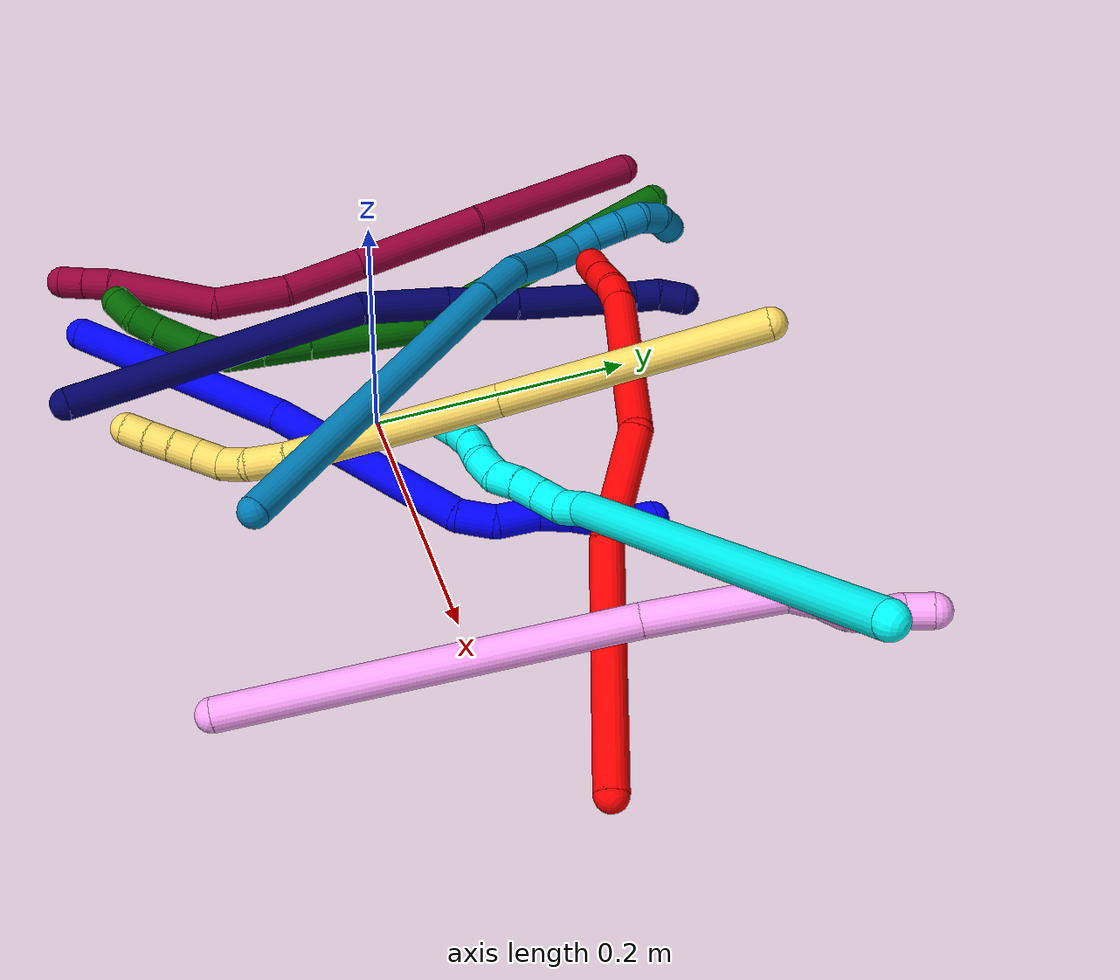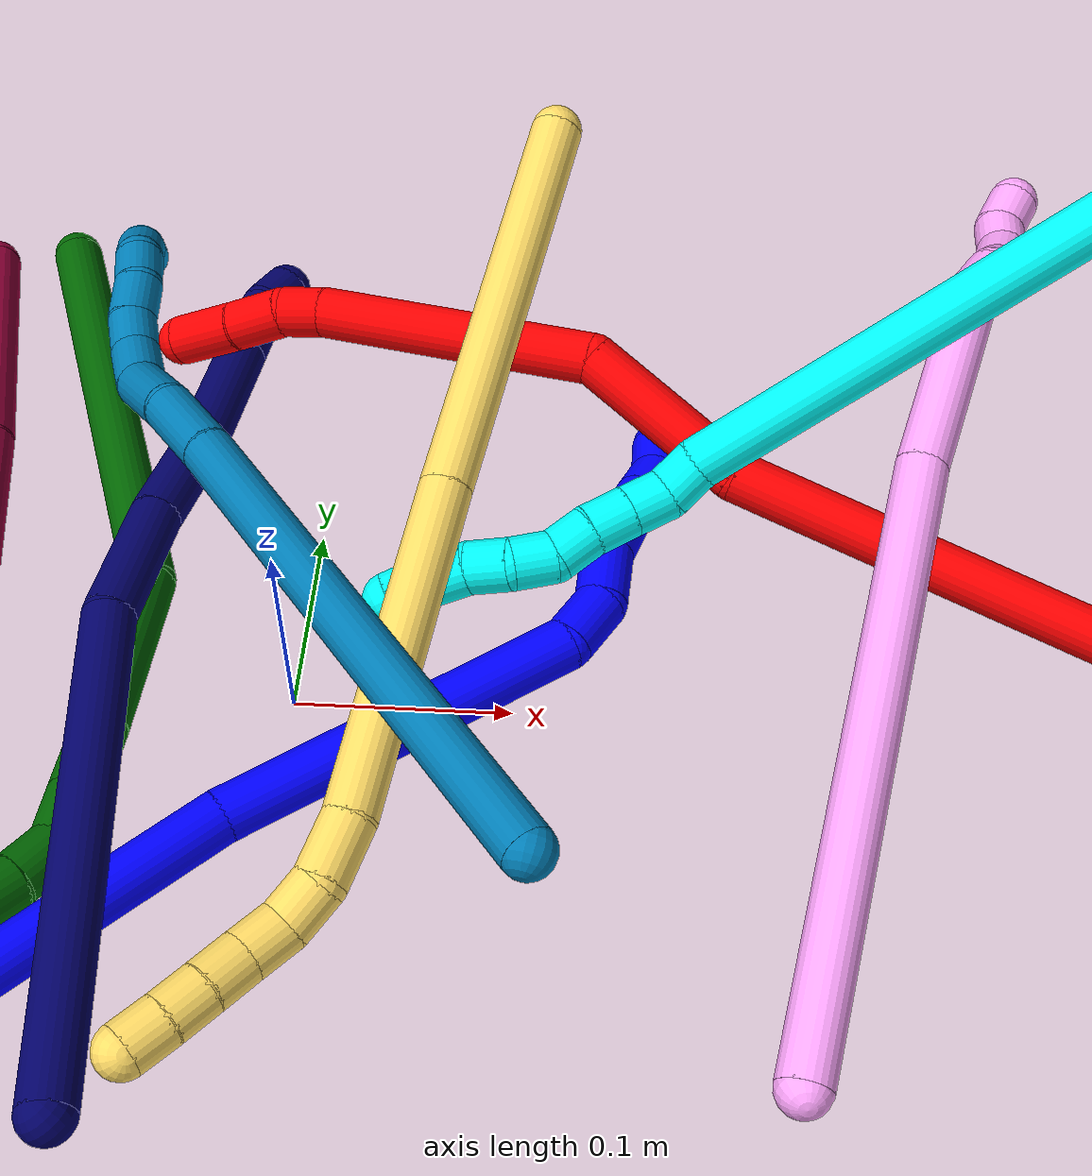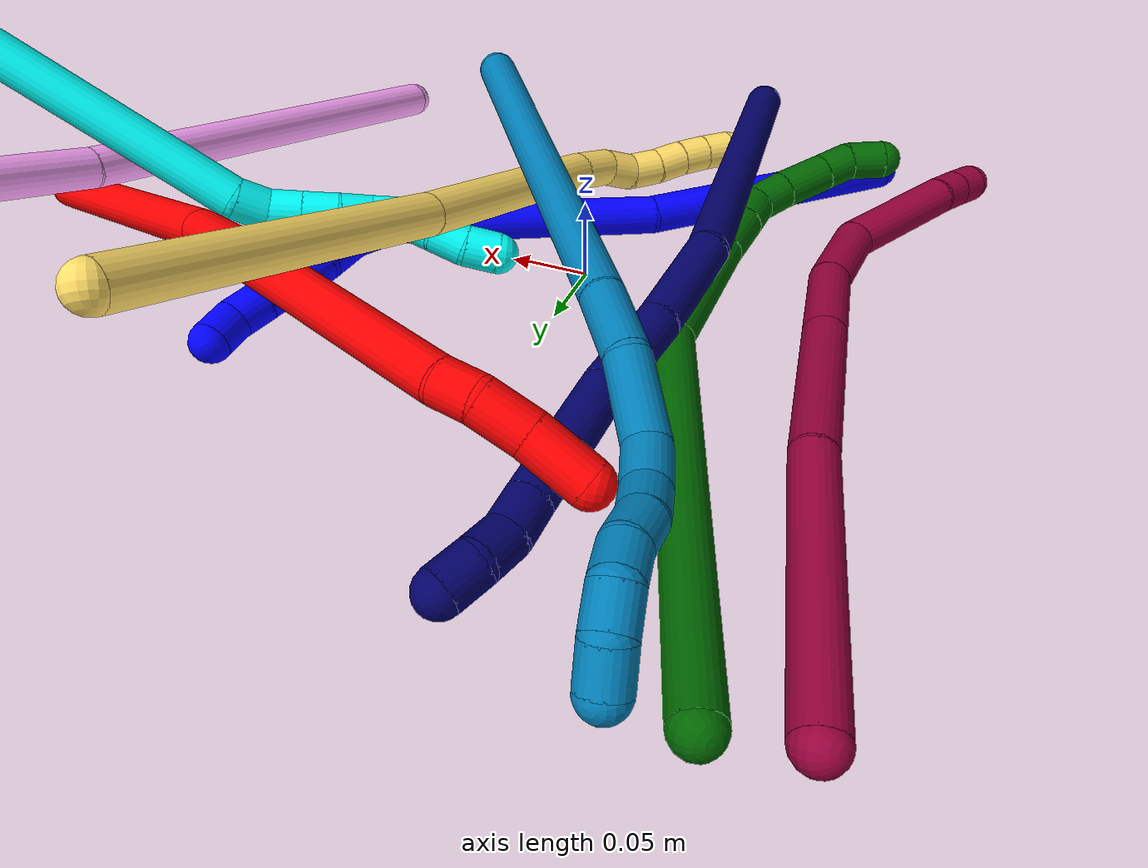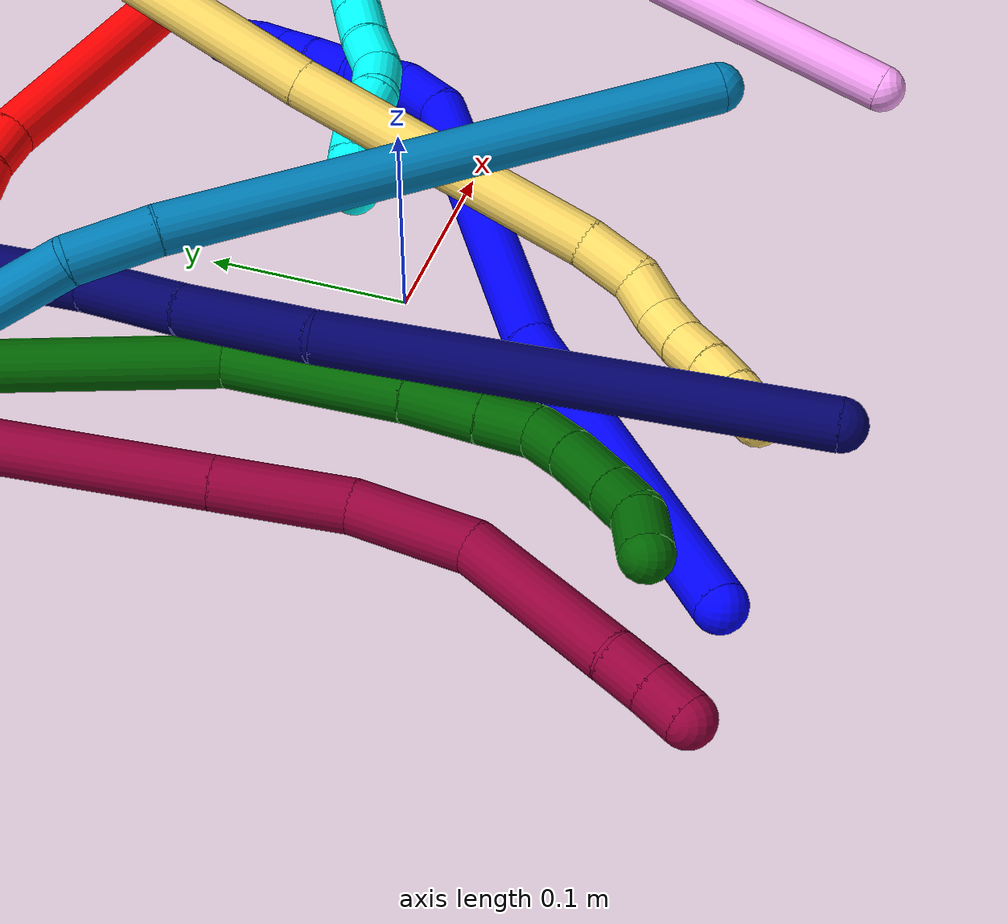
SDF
<sdf version="1.7">
 <world name="default">
  <plugin name="TubeGeneratorPlugin" filename="libtube_generator_plugin.so"/>
  <model name="photoneo_s_sensor">
   <static>1</static>
   <pose>0 0 2 1.57079 1.57079 3.14159</pose>
   <link name="link">
    <inertial><mass>0.1</mass></inertial>
    <sensor name="sensor" type="depth">
     <update_rate>30</update_rate>
     <camera>
      <horizontal_fov>1.22</horizontal_fov>
      <image><width>1920</width><height>1200</height><format>B8G8R8</format></image>
      <clip><near>0.1</near><far>4</far></clip>
      <depth_camera><output>points</output></depth_camera>
     </camera>
     <plugin name="camera_plugin" filename="libgazebo_ros_depth_camera.so">
      <baseline>0.2</baseline>
      <alwaysOn>1</alwaysOn>
      <updateRate>0.0</updateRate>
      <cameraName>camera_ir</cameraName>
      <imageTopicName>/camera/color/image_raw</imageTopicName>
      <cameraInfoTopicName>/camera/color/camera_info</cameraInfoTopicName>
      <depthImageTopicName>/camera/depth/image_raw</depthImageTopicName>
      <depthImageCameraInfoTopicName>/camera/depth/camera_info</depthImageCameraInfoTopicName>
      <pointCloudTopicName>/camera/depth/points</pointCloudTopicName>
      <frameName>fr_optical</frameName>
      <pointCloudCutoff>0.1</pointCloudCutoff>
      <pointCloudCutoffMax>2.0</pointCloudCutoffMax>
      <distortionK1>0</distortionK1>
      <distortionK2>0</distortionK2>
      <distortionK3>0</distortionK3>
      <distortionT1>0</distortionT1>
      <distortionT2>0</distortionT2>
      <CxPrime>0</CxPrime>
      <Cx>0</Cx>
      <Cy>0</Cy>
      <focalLength>0</focalLength>
      <hackBaseline>0</hackBaseline>
     </plugin>
    </sensor>
   </link>
  </model>
  <gravity>0 0 -9.8</gravity>
  <magnetic_field>6e-06 2.3e-05 -4.2e-05</magnetic_field>
  <atmosphere type="adiabatic"/>
  <physics name="default_physics" default="0" type="ode">
   <max_step_size>0.003</max_step_size>
   <real_time_factor>1</real_time_factor>
   <real_time_update_rate>1000</real_time_update_rate>
   <max_contacts>10000</max_contacts>
   <ode>
    <solver>
     <type>quick</type>
     <iters>100</iters>
     <sor>1.3</sor>
     <use_dynamic_moi_rescaling>0</use_dynamic_moi_rescaling>
    </solver>
    <constraints>
     <contact_max_correcting_vel>0</contact_max_correcting_vel>
     <contact_surface_layer>0.001</contact_surface_layer>
     <cfm>0</cfm>
     <erp>0.2</erp>
    </constraints>
   </ode>
  </physics>
  <scene><ambient>0.4 0.4 0.4 1</ambient><background>0.7 0.7 0.7 1</background><shadows>0</shadows></scene>
  <audio><device>default</device></audio>
  <spherical_coordinates>
   <surface_model>EARTH_WGS84</surface_model>
   <latitude_deg>0</latitude_deg>
   <longitude_deg>0</longitude_deg>
   <elevation>0</elevation>
   <heading_deg>0</heading_deg>
  </spherical_coordinates>
  <model name="bin">
   <static>1</static>
   <link name="bottom">
    <collision name="collision-bottom">
     <pose>0 0 -0.01 0 -0 0</pose>
     <geometry><box><size>0.8 0.6 0.02</size></box></geometry>
     <surface>
      <friction><ode><mu>100</mu><mu2>100</mu2></ode></friction>
      <contact><collide_bitmask>65535</collide_bitmask></contact>
     </surface>
    </collision>
   </link>
   <link name="west_wall">
    <collision name="collision-west_wall">
     <pose>-0.41 0 0.1 0 -0 0</pose>
     <geometry><box><size>0.02 0.6 0.2</size></box></geometry>
     <surface>
      <friction><ode><mu>100</mu><mu2>100</mu2></ode></friction>
      <contact><collide_bitmask>65535</collide_bitmask></contact>
     </surface>
    </collision>
   </link>
   <link name="east_wall">
    <collision name="collision-east_wall">
     <pose>0.41 0 0.1 0 -0 0</pose>
     <geometry><box><size>0.02 0.6 0.2</size></box></geometry>
     <surface>
      <friction><ode><mu>100</mu><mu2>100</mu2></ode></friction>
      <contact><collide_bitmask>65535</collide_bitmask></contact>
     </surface>
    </collision>
   </link>
   <link name="south_wall">
    <collision name="collision-south_wall">
     <pose>0 -0.31 0.1 0 -0 0</pose>
     <geometry><box><size>0.8 0.02 0.2</size></box></geometry>
     <surface>
      <friction><ode><mu>100</mu><mu2>100</mu2></ode></friction>
      <contact><collide_bitmask>65535</collide_bitmask></contact>
     </surface>
    </collision>
   </link>
   <link name="north_wall">
    <collision name="collision-north_wall">
     <pose>0 0.31 0.1 0 -0 0</pose>
     <geometry><box><size>0.8 0.02 0.2</size></box></geometry>
     <surface>
      <friction><ode><mu>100</mu><mu2>100</mu2></ode></friction>
      <contact><collide_bitmask>65535</collide_bitmask></contact>
     </surface>
    </collision>
   </link>
  </model>
  <model name="1">
   <static>0</static>
   <link name="1">
    <collision name="collision-cylinder-e_1_1_4">
     <pose>0.064473 0.060975 0.019854 -1.25601 0.788096 -0.586387</pose>
     <geometry><cylinder><radius>0.0125</radius><length>0.181867</length></cylinder></geometry>
     <surface>
      <friction><ode><mu>1.16</mu><mu2>1.16</mu2><slip1>0</slip1><slip2>0</slip2></ode></friction>
      <contact><ode><kp>1e+06</kp><kd>1</kd><max_vel>0</max_vel><min_depth>0.001</min_depth></ode></contact>
     </surface>
    </collision>
    <visual name="visual-cylinder-e_1_1_4">
     <pose>0.064473 0.060975 0.019854 -1.25601 0.788096 -0.586387</pose>
     <geometry><cylinder><radius>0.0125</radius><length>0.181867</length></cylinder></geometry>
     <material><ambient>0 0 1 1</ambient></material>
    </visual>
    <collision name="collision-cylinder-e_2_4_5">
     <pose>0.197436 0.174737 0.044534 -1.47963 0.91215 -0.841994</pose>
     <geometry><cylinder><radius>0.0125</radius><length>0.173214</length></cylinder></geometry>
     <surface>
      <friction><ode><mu>1.16</mu><mu2>1.16</mu2><slip1>0</slip1><slip2>0</slip2></ode></friction>
      <contact><ode><kp>1e+06</kp><kd>1</kd><max_vel>0</max_vel><min_depth>0.001</min_depth></ode></contact>
     </surface>
    </collision>
    <visual name="visual-cylinder-e_2_4_5">
     <pose>0.197436 0.174737 0.044534 -1.47963 0.91215 -0.841994</pose>
     <geometry><cylinder><radius>0.0125</radius><length>0.173214</length></cylinder></geometry>
     <material><ambient>0 0 1 1</ambient></material>
    </visual>
    <collision name="collision-cylinder-e_3_5_6">
     <pose>0.274226 0.236633 0.056025 -0.939054 0.634003 -0.329877</pose>
     <geometry><cylinder><radius>0.0125</radius><length>0.02802</length></cylinder></geometry>
     <surface>
      <friction><ode><mu>1.16</mu><mu2>1.16</mu2><slip1>0</slip1><slip2>0</slip2></ode></friction>
      <contact><ode><kp>1e+06</kp><kd>1</kd><max_vel>0</max_vel><min_depth>0.001</min_depth></ode></contact>
     </surface>
    </collision>
    <visual name="visual-cylinder-e_3_5_6">
     <pose>0.274226 0.236633 0.056025 -0.939054 0.634003 -0.329877</pose>
     <geometry><cylinder><radius>0.0125</radius><length>0.02802</length></cylinder></geometry>
     <material><ambient>0 0 1 1</ambient></material>
    </visual>
    <collision name="collision-cylinder-e_4_6_7">
     <pose>0.287438 0.253365 0.075383 -0.540887 0.320422 -0.08954</pose>
     <geometry><cylinder><radius>0.0125</radius><length>0.031199</length></cylinder></geometry>
     <surface>
      <friction><ode><mu>1.16</mu><mu2>1.16</mu2><slip1>0</slip1><slip2>0</slip2></ode></friction>
      <contact><ode><kp>1e+06</kp><kd>1</kd><max_vel>0</max_vel><min_depth>0.001</min_depth></ode></contact>
     </surface>
    </collision>
    <visual name="visual-cylinder-e_4_6_7">
     <pose>0.287438 0.253365 0.075383 -0.540887 0.320422 -0.08954</pose>
     <geometry><cylinder><radius>0.0125</radius><length>0.031199</length></cylinder></geometry>
     <material><ambient>0 0 1 1</ambient></material>
    </visual>
    <collision name="collision-cylinder-e_5_7_8">
     <pose>0.297563 0.268978 0.095919 -0.794563 0.435598 -0.185189</pose>
     <geometry><cylinder><radius>0.0125</radius><length>0.0247</length></cylinder></geometry>
     <surface>
      <friction><ode><mu>1.16</mu><mu2>1.16</mu2><slip1>0</slip1><slip2>0</slip2></ode></friction>
      <contact><ode><kp>1e+06</kp><kd>1</kd><max_vel>0</max_vel><min_depth>0.001</min_depth></ode></contact>
     </surface>
    </collision>
    <visual name="visual-cylinder-e_5_7_8">
     <pose>0.297563 0.268978 0.095919 -0.794563 0.435598 -0.185189</pose>
     <geometry><cylinder><radius>0.0125</radius><length>0.0247</length></cylinder></geometry>
     <material><ambient>0 0 1 1</ambient></material>
    </visual>
    <collision name="collision-cylinder-e_6_8_9">
     <pose>0.306645 0.284376 0.10953 -0.909426 0.391168 -0.193109</pose>
     <geometry><cylinder><radius>0.0125</radius><length>0.020309</length></cylinder></geometry>
     <surface>
      <friction><ode><mu>1.16</mu><mu2>1.16</mu2><slip1>0</slip1><slip2>0</slip2></ode></friction>
      <contact><ode><kp>1e+06</kp><kd>1</kd><max_vel>0</max_vel><min_depth>0.001</min_depth></ode></contact>
     </surface>
    </collision>
    <visual name="visual-cylinder-e_6_8_9">
     <pose>0.306645 0.284376 0.10953 -0.909426 0.391168 -0.193109</pose>
     <geometry><cylinder><radius>0.0125</radius><length>0.020309</length></cylinder></geometry>
     <material><ambient>0 0 1 1</ambient></material>
    </visual>
    <collision name="collision-cylinder-e_7_9_10">
     <pose>0.314573 0.299069 0.120898 -0.915164 0.415627 -0.206928</pose>
     <geometry><cylinder><radius>0.0125</radius><length>0.020091</length></cylinder></geometry>
     <surface>
      <friction><ode><mu>1.16</mu><mu2>1.16</mu2><slip1>0</slip1><slip2>0</slip2></ode></friction>
      <contact><ode><kp>1e+06</kp><kd>1</kd><max_vel>0</max_vel><min_depth>0.001</min_depth></ode></contact>
     </surface>
    </collision>
    <visual name="visual-cylinder-e_7_9_10">
     <pose>0.314573 0.299069 0.120898 -0.915164 0.415627 -0.206928</pose>
     <geometry><cylinder><radius>0.0125</radius><length>0.020091</length></cylinder></geometry>
     <material><ambient>0 0 1 1</ambient></material>
    </visual>
    <collision name="collision-cylinder-e_8_10_2">
     <pose>0.320958 0.311724 0.134977 -0.564794 0.228113 -0.066451</pose>
     <geometry><cylinder><radius>0.0125</radius><length>0.020601</length></cylinder></geometry>
     <surface>
      <friction><ode><mu>1.16</mu><mu2>1.16</mu2><slip1>0</slip1><slip2>0</slip2></ode></friction>
      <contact><ode><kp>1e+06</kp><kd>1</kd><max_vel>0</max_vel><min_depth>0.001</min_depth></ode></contact>
     </surface>
    </collision>
    <visual name="visual-cylinder-e_8_10_2">
     <pose>0.320958 0.311724 0.134977 -0.564794 0.228113 -0.066451</pose>
     <geometry><cylinder><radius>0.0125</radius><length>0.020601</length></cylinder></geometry>
     <material><ambient>0 0 1 1</ambient></material>
    </visual>
    <collision name="collision-sphere-2">
     <pose>0.323288 0.317094 0.143452 0 -0 0</pose>
     <geometry><sphere><radius>0.0125</radius></sphere></geometry>
     <surface>
      <friction><ode><mu>1.16</mu><mu2>1.16</mu2><slip1>0</slip1><slip2>0</slip2></ode></friction>
      <contact><ode><kp>1e+06</kp><kd>1</kd><max_vel>0</max_vel><min_depth>0.001</min_depth></ode></contact>
     </surface>
    </collision>
    <visual name="visual-sphere-2">
     <pose>0.323288 0.317094 0.143452 0 -0 0</pose>
     <geometry><sphere><radius>0.0125</radius></sphere></geometry>
     <material><ambient>0 0 1 1</ambient></material>
    </visual>
    <collision name="collision-sphere-10">
     <pose>0.318629 0.306354 0.126501 0 -0 0</pose>
     <geometry><sphere><radius>0.0125</radius></sphere></geometry>
     <surface>
      <friction><ode><mu>1.16</mu><mu2>1.16</mu2><slip1>0</slip1><slip2>0</slip2></ode></friction>
      <contact><ode><kp>1e+06</kp><kd>1</kd><max_vel>0</max_vel><min_depth>0.001</min_depth></ode></contact>
     </surface>
    </collision>
    <visual name="visual-sphere-10">
     <pose>0.318629 0.306354 0.126501 0 -0 0</pose>
     <geometry><sphere><radius>0.0125</radius></sphere></geometry>
     <material><ambient>0 0 1 1</ambient></material>
    </visual>
    <collision name="collision-sphere-9">
     <pose>0.310517 0.291784 0.115295 0 -0 0</pose>
     <geometry><sphere><radius>0.0125</radius></sphere></geometry>
     <surface>
      <friction><ode><mu>1.16</mu><mu2>1.16</mu2><slip1>0</slip1><slip2>0</slip2></ode></friction>
      <contact><ode><kp>1e+06</kp><kd>1</kd><max_vel>0</max_vel><min_depth>0.001</min_depth></ode></contact>
     </surface>
    </collision>
    <visual name="visual-sphere-9">
     <pose>0.310517 0.291784 0.115295 0 -0 0</pose>
     <geometry><sphere><radius>0.0125</radius></sphere></geometry>
     <material><ambient>0 0 1 1</ambient></material>
    </visual>
    <collision name="collision-sphere-4">
     <pose>0.128946 0.12195 0.039708 0 -0 0</pose>
     <geometry><sphere><radius>0.0125</radius></sphere></geometry>
     <surface>
      <friction><ode><mu>1.16</mu><mu2>1.16</mu2><slip1>0</slip1><slip2>0</slip2></ode></friction>
      <contact><ode><kp>1e+06</kp><kd>1</kd><max_vel>0</max_vel><min_depth>0.001</min_depth></ode></contact>
     </surface>
    </collision>
    <visual name="visual-sphere-4">
     <pose>0.128946 0.12195 0.039708 0 -0 0</pose>
     <geometry><sphere><radius>0.0125</radius></sphere></geometry>
     <material><ambient>0 0 1 1</ambient></material>
    </visual>
    <collision name="collision-sphere-1">
     <geometry><sphere><radius>0.0125</radius></sphere></geometry>
     <surface>
      <friction><ode><mu>1.16</mu><mu2>1.16</mu2><slip1>0</slip1><slip2>0</slip2></ode></friction>
      <contact><ode><kp>1e+06</kp><kd>1</kd><max_vel>0</max_vel><min_depth>0.001</min_depth></ode></contact>
     </surface>
    </collision>
    <visual name="visual-sphere-1">
     <geometry><sphere><radius>0.0125</radius></sphere></geometry>
     <material><ambient>0 0 1 1</ambient></material>
    </visual>
    <collision name="collision-sphere-8">
     <pose>0.302774 0.276968 0.103764 0 -0 0</pose>
     <geometry><sphere><radius>0.0125</radius></sphere></geometry>
     <surface>
      <friction><ode><mu>1.16</mu><mu2>1.16</mu2><slip1>0</slip1><slip2>0</slip2></ode></friction>
      <contact><ode><kp>1e+06</kp><kd>1</kd><max_vel>0</max_vel><min_depth>0.001</min_depth></ode></contact>
     </surface>
    </collision>
    <visual name="visual-sphere-8">
     <pose>0.302774 0.276968 0.103764 0 -0 0</pose>
     <geometry><sphere><radius>0.0125</radius></sphere></geometry>
     <material><ambient>0 0 1 1</ambient></material>
    </visual>
    <collision name="collision-sphere-5">
     <pose>0.265927 0.227524 0.049359 0 -0 0</pose>
     <geometry><sphere><radius>0.0125</radius></sphere></geometry>
     <surface>
      <friction><ode><mu>1.16</mu><mu2>1.16</mu2><slip1>0</slip1><slip2>0</slip2></ode></friction>
      <contact><ode><kp>1e+06</kp><kd>1</kd><max_vel>0</max_vel><min_depth>0.001</min_depth></ode></contact>
     </surface>
    </collision>
    <visual name="visual-sphere-5">
     <pose>0.265927 0.227524 0.049359 0 -0 0</pose>
     <geometry><sphere><radius>0.0125</radius></sphere></geometry>
     <material><ambient>0 0 1 1</ambient></material>
    </visual>
    <collision name="collision-sphere-6">
     <pose>0.282525 0.245742 0.062691 0 -0 0</pose>
     <geometry><sphere><radius>0.0125</radius></sphere></geometry>
     <surface>
      <friction><ode><mu>1.16</mu><mu2>1.16</mu2><slip1>0</slip1><slip2>0</slip2></ode></friction>
      <contact><ode><kp>1e+06</kp><kd>1</kd><max_vel>0</max_vel><min_depth>0.001</min_depth></ode></contact>
     </surface>
    </collision>
    <visual name="visual-sphere-6">
     <pose>0.282525 0.245742 0.062691 0 -0 0</pose>
     <geometry><sphere><radius>0.0125</radius></sphere></geometry>
     <material><ambient>0 0 1 1</ambient></material>
    </visual>
    <collision name="collision-sphere-7">
     <pose>0.292352 0.260989 0.088075 0 -0 0</pose>
     <geometry><sphere><radius>0.0125</radius></sphere></geometry>
     <surface>
      <friction><ode><mu>1.16</mu><mu2>1.16</mu2><slip1>0</slip1><slip2>0</slip2></ode></friction>
      <contact><ode><kp>1e+06</kp><kd>1</kd><max_vel>0</max_vel><min_depth>0.001</min_depth></ode></contact>
     </surface>
    </collision>
    <visual name="visual-sphere-7">
     <pose>0.292352 0.260989 0.088075 0 -0 0</pose>
     <geometry><sphere><radius>0.0125</radius></sphere></geometry>
     <material><ambient>0 0 1 1</ambient></material>
    </visual>
    <inertial>
     <pose>0.17817 0.161482 0.050099 0 -0 0</pose>
     <mass>0.5</mass>
     <inertia>
      <ixx>0.000114</ixx>
      <ixy>0</ixy>
      <ixz>0</ixz>
      <iyy>0.00024</iyy>
      <iyz>0</iyz>
      <izz>-0.00132</izz>
     </inertia>
    </inertial>
   </link>
   <pose>-0.15177 -0.19649 0.011555 -1.31333 -0.696046 0.372297</pose>
  </model>
  <model name="2">
   <static>0</static>
   <link name="2">
    <collision name="collision-cylinder-e_1_1_4">
     <pose>-0.05397 -0.010744 -0.075276 2.99982 -0.617257 -2.70331</pose>
     <geometry><cylinder><radius>0.0125</radius><length>0.18649</length></cylinder></geometry>
     <surface>
      <friction><ode><mu>1.16</mu><mu2>1.16</mu2><slip1>0</slip1><slip2>0</slip2></ode></friction>
      <contact><ode><kp>1e+06</kp><kd>1</kd><max_vel>0</max_vel><min_depth>0.001</min_depth></ode></contact>
     </surface>
    </collision>
    <visual name="visual-cylinder-e_1_1_4">
     <pose>-0.05397 -0.010744 -0.075276 2.99982 -0.617257 -2.70331</pose>
     <geometry><cylinder><radius>0.0125</radius><length>0.18649</length></cylinder></geometry>
     <material><ambient>1 0 0 1</ambient></material>
    </visual>
    <collision name="collision-cylinder-e_2_4_5">
     <pose>-0.142356 -0.026135 -0.177672 2.97191 -0.896346 -2.79144</pose>
     <geometry><cylinder><radius>0.0125</radius><length>0.088125</length></cylinder></geometry>
     <surface>
      <friction><ode><mu>1.16</mu><mu2>1.16</mu2><slip1>0</slip1><slip2>0</slip2></ode></friction>
      <contact><ode><kp>1e+06</kp><kd>1</kd><max_vel>0</max_vel><min_depth>0.001</min_depth></ode></contact>
     </surface>
    </collision>
    <visual name="visual-cylinder-e_2_4_5">
     <pose>-0.142356 -0.026135 -0.177672 2.97191 -0.896346 -2.79144</pose>
     <geometry><cylinder><radius>0.0125</radius><length>0.088125</length></cylinder></geometry>
     <material><ambient>1 0 0 1</ambient></material>
    </visual>
    <collision name="collision-cylinder-e_3_5_6">
     <pose>-0.207135 -0.022208 -0.268636 -3.00811 -0.440484 2.5613</pose>
     <geometry><cylinder><radius>0.0125</radius><length>0.142429</length></cylinder></geometry>
     <surface>
      <friction><ode><mu>1.16</mu><mu2>1.16</mu2><slip1>0</slip1><slip2>0</slip2></ode></friction>
      <contact><ode><kp>1e+06</kp><kd>1</kd><max_vel>0</max_vel><min_depth>0.001</min_depth></ode></contact>
     </surface>
    </collision>
    <visual name="visual-cylinder-e_3_5_6">
     <pose>-0.207135 -0.022208 -0.268636 -3.00811 -0.440484 2.5613</pose>
     <geometry><cylinder><radius>0.0125</radius><length>0.142429</length></cylinder></geometry>
     <material><ambient>1 0 0 1</ambient></material>
    </visual>
    <collision name="collision-cylinder-e_4_6_7">
     <pose>-0.240299 -0.012901 -0.342713 -3.06994 -0.266404 2.61884</pose>
     <geometry><cylinder><radius>0.0125</radius><length>0.021269</length></cylinder></geometry>
     <surface>
      <friction><ode><mu>1.16</mu><mu2>1.16</mu2><slip1>0</slip1><slip2>0</slip2></ode></friction>
      <contact><ode><kp>1e+06</kp><kd>1</kd><max_vel>0</max_vel><min_depth>0.001</min_depth></ode></contact>
     </surface>
    </collision>
    <visual name="visual-cylinder-e_4_6_7">
     <pose>-0.240299 -0.012901 -0.342713 -3.06994 -0.266404 2.61884</pose>
     <geometry><cylinder><radius>0.0125</radius><length>0.021269</length></cylinder></geometry>
     <material><ambient>1 0 0 1</ambient></material>
    </visual>
    <collision name="collision-cylinder-e_5_7_8">
     <pose>-0.243841 -0.008233 -0.366135 -2.85176 -0.053873 0.365127</pose>
     <geometry><cylinder><radius>0.0125</radius><length>0.027567</length></cylinder></geometry>
     <surface>
      <friction><ode><mu>1.16</mu><mu2>1.16</mu2><slip1>0</slip1><slip2>0</slip2></ode></friction>
      <contact><ode><kp>1e+06</kp><kd>1</kd><max_vel>0</max_vel><min_depth>0.001</min_depth></ode></contact>
     </surface>
    </collision>
    <visual name="visual-cylinder-e_5_7_8">
     <pose>-0.243841 -0.008233 -0.366135 -2.85176 -0.053873 0.365127</pose>
     <geometry><cylinder><radius>0.0125</radius><length>0.027567</length></cylinder></geometry>
     <material><ambient>1 0 0 1</ambient></material>
    </visual>
    <collision name="collision-cylinder-e_6_8_2">
     <pose>-0.246553 0.001855 -0.395113 -2.76989 -0.115688 0.597538</pose>
     <geometry><cylinder><radius>0.0125</radius><length>0.034119</length></cylinder></geometry>
     <surface>
      <friction><ode><mu>1.16</mu><mu2>1.16</mu2><slip1>0</slip1><slip2>0</slip2></ode></friction>
      <contact><ode><kp>1e+06</kp><kd>1</kd><max_vel>0</max_vel><min_depth>0.001</min_depth></ode></contact>
     </surface>
    </collision>
    <visual name="visual-cylinder-e_6_8_2">
     <pose>-0.246553 0.001855 -0.395113 -2.76989 -0.115688 0.597538</pose>
     <geometry><cylinder><radius>0.0125</radius><length>0.034119</length></cylinder></geometry>
     <material><ambient>1 0 0 1</ambient></material>
    </visual>
    <collision name="collision-sphere-2">
     <pose>-0.248522 0.00801 -0.410902 0 -0 0</pose>
     <geometry><sphere><radius>0.0125</radius></sphere></geometry>
     <surface>
      <friction><ode><mu>1.16</mu><mu2>1.16</mu2><slip1>0</slip1><slip2>0</slip2></ode></friction>
      <contact><ode><kp>1e+06</kp><kd>1</kd><max_vel>0</max_vel><min_depth>0.001</min_depth></ode></contact>
     </surface>
    </collision>
    <visual name="visual-sphere-2">
     <pose>-0.248522 0.00801 -0.410902 0 -0 0</pose>
     <geometry><sphere><radius>0.0125</radius></sphere></geometry>
     <material><ambient>1 0 0 1</ambient></material>
    </visual>
    <collision name="collision-sphere-4">
     <pose>-0.107941 -0.021488 -0.150551 0 -0 0</pose>
     <geometry><sphere><radius>0.0125</radius></sphere></geometry>
     <surface>
      <friction><ode><mu>1.16</mu><mu2>1.16</mu2><slip1>0</slip1><slip2>0</slip2></ode></friction>
      <contact><ode><kp>1e+06</kp><kd>1</kd><max_vel>0</max_vel><min_depth>0.001</min_depth></ode></contact>
     </surface>
    </collision>
    <visual name="visual-sphere-4">
     <pose>-0.107941 -0.021488 -0.150551 0 -0 0</pose>
     <geometry><sphere><radius>0.0125</radius></sphere></geometry>
     <material><ambient>1 0 0 1</ambient></material>
    </visual>
    <collision name="collision-sphere-1">
     <geometry><sphere><radius>0.0125</radius></sphere></geometry>
     <surface>
      <friction><ode><mu>1.16</mu><mu2>1.16</mu2><slip1>0</slip1><slip2>0</slip2></ode></friction>
      <contact><ode><kp>1e+06</kp><kd>1</kd><max_vel>0</max_vel><min_depth>0.001</min_depth></ode></contact>
     </surface>
    </collision>
    <visual name="visual-sphere-1">
     <geometry><sphere><radius>0.0125</radius></sphere></geometry>
     <material><ambient>1 0 0 1</ambient></material>
    </visual>
    <collision name="collision-sphere-8">
     <pose>-0.244583 -0.004299 -0.379325 0 -0 0</pose>
     <geometry><sphere><radius>0.0125</radius></sphere></geometry>
     <surface>
      <friction><ode><mu>1.16</mu><mu2>1.16</mu2><slip1>0</slip1><slip2>0</slip2></ode></friction>
      <contact><ode><kp>1e+06</kp><kd>1</kd><max_vel>0</max_vel><min_depth>0.001</min_depth></ode></contact>
     </surface>
    </collision>
    <visual name="visual-sphere-8">
     <pose>-0.244583 -0.004299 -0.379325 0 -0 0</pose>
     <geometry><sphere><radius>0.0125</radius></sphere></geometry>
     <material><ambient>1 0 0 1</ambient></material>
    </visual>
    <collision name="collision-sphere-5">
     <pose>-0.176771 -0.030782 -0.204792 0 -0 0</pose>
     <geometry><sphere><radius>0.0125</radius></sphere></geometry>
     <surface>
      <friction><ode><mu>1.16</mu><mu2>1.16</mu2><slip1>0</slip1><slip2>0</slip2></ode></friction>
      <contact><ode><kp>1e+06</kp><kd>1</kd><max_vel>0</max_vel><min_depth>0.001</min_depth></ode></contact>
     </surface>
    </collision>
    <visual name="visual-sphere-5">
     <pose>-0.176771 -0.030782 -0.204792 0 -0 0</pose>
     <geometry><sphere><radius>0.0125</radius></sphere></geometry>
     <material><ambient>1 0 0 1</ambient></material>
    </visual>
    <collision name="collision-sphere-6">
     <pose>-0.2375 -0.013635 -0.33248 0 -0 0</pose>
     <geometry><sphere><radius>0.0125</radius></sphere></geometry>
     <surface>
      <friction><ode><mu>1.16</mu><mu2>1.16</mu2><slip1>0</slip1><slip2>0</slip2></ode></friction>
      <contact><ode><kp>1e+06</kp><kd>1</kd><max_vel>0</max_vel><min_depth>0.001</min_depth></ode></contact>
     </surface>
    </collision>
    <visual name="visual-sphere-6">
     <pose>-0.2375 -0.013635 -0.33248 0 -0 0</pose>
     <geometry><sphere><radius>0.0125</radius></sphere></geometry>
     <material><ambient>1 0 0 1</ambient></material>
    </visual>
    <collision name="collision-sphere-7">
     <pose>-0.243099 -0.012166 -0.352946 0 -0 0</pose>
     <geometry><sphere><radius>0.0125</radius></sphere></geometry>
     <surface>
      <friction><ode><mu>1.16</mu><mu2>1.16</mu2><slip1>0</slip1><slip2>0</slip2></ode></friction>
      <contact><ode><kp>1e+06</kp><kd>1</kd><max_vel>0</max_vel><min_depth>0.001</min_depth></ode></contact>
     </surface>
    </collision>
    <visual name="visual-sphere-7">
     <pose>-0.243099 -0.012166 -0.352946 0 -0 0</pose>
     <geometry><sphere><radius>0.0125</radius></sphere></geometry>
     <material><ambient>1 0 0 1</ambient></material>
    </visual>
    <inertial>
     <pose>-0.144715 -0.015816 -0.197641 0 -0 0</pose>
     <mass>0.5</mass>
     <inertia>
      <ixx>-0.000717</ixx>
      <ixy>0</ixy>
      <ixz>0</ixz>
      <iyy>0.000701</iyy>
      <iyz>0</iyz>
      <izz>0.000476</izz>
     </inertia>
    </inertial>
   </link>
   <pose>0.370626 0.050035 0.011492 -1.35443 0.442489 -1.31072</pose>
  </model>
  <model name="3">
   <static>0</static>
   <link name="3">
    <collision name="collision-cylinder-e_1_1_4">
     <pose>-0.031185 0.065363 -0.15321 -2.73835 -0.185074 0.852391</pose>
     <geometry><cylinder><radius>0.0125</radius><length>0.338928</length></cylinder></geometry>
     <surface>
      <friction><ode><mu>1.16</mu><mu2>1.16</mu2><slip1>0</slip1><slip2>0</slip2></ode></friction>
      <contact><ode><kp>1e+06</kp><kd>1</kd><max_vel>0</max_vel><min_depth>0.001</min_depth></ode></contact>
     </surface>
    </collision>
    <visual name="visual-cylinder-e_1_1_4">
     <pose>-0.031185 0.065363 -0.15321 -2.73835 -0.185074 0.852391</pose>
     <geometry><cylinder><radius>0.0125</radius><length>0.338928</length></cylinder></geometry>
     <material><ambient>0.003922 1 0.996078 1</ambient></material>
    </visual>
    <collision name="collision-cylinder-e_2_4_5">
     <pose>-0.060937 0.133857 -0.315808 -2.81961 0.143739 -0.834564</pose>
     <geometry><cylinder><radius>0.0125</radius><length>0.02</length></cylinder></geometry>
     <surface>
      <friction><ode><mu>1.16</mu><mu2>1.16</mu2><slip1>0</slip1><slip2>0</slip2></ode></friction>
      <contact><ode><kp>1e+06</kp><kd>1</kd><max_vel>0</max_vel><min_depth>0.001</min_depth></ode></contact>
     </surface>
    </collision>
    <visual name="visual-cylinder-e_2_4_5">
     <pose>-0.060937 0.133857 -0.315808 -2.81961 0.143739 -0.834564</pose>
     <geometry><cylinder><radius>0.0125</radius><length>0.02</length></cylinder></geometry>
     <material><ambient>0.003922 1 0.996078 1</ambient></material>
    </visual>
    <collision name="collision-cylinder-e_3_5_6">
     <pose>-0.059202 0.136248 -0.335167 3.06745 0.030203 0.773432</pose>
     <geometry><cylinder><radius>0.0125</radius><length>0.020004</length></cylinder></geometry>
     <surface>
      <friction><ode><mu>1.16</mu><mu2>1.16</mu2><slip1>0</slip1><slip2>0</slip2></ode></friction>
      <contact><ode><kp>1e+06</kp><kd>1</kd><max_vel>0</max_vel><min_depth>0.001</min_depth></ode></contact>
     </surface>
    </collision>
    <visual name="visual-cylinder-e_3_5_6">
     <pose>-0.059202 0.136248 -0.335167 3.06745 0.030203 0.773432</pose>
     <geometry><cylinder><radius>0.0125</radius><length>0.020004</length></cylinder></geometry>
     <material><ambient>0.003922 1 0.996078 1</ambient></material>
    </visual>
    <collision name="collision-cylinder-e_4_6_7">
     <pose>-0.058445 0.134765 -0.355413 3.06947 0.044137 1.09811</pose>
     <geometry><cylinder><radius>0.0125</radius><length>0.020627</length></cylinder></geometry>
     <surface>
      <friction><ode><mu>1.16</mu><mu2>1.16</mu2><slip1>0</slip1><slip2>0</slip2></ode></friction>
      <contact><ode><kp>1e+06</kp><kd>1</kd><max_vel>0</max_vel><min_depth>0.001</min_depth></ode></contact>
     </surface>
    </collision>
    <visual name="visual-cylinder-e_4_6_7">
     <pose>-0.058445 0.134765 -0.355413 3.06947 0.044137 1.09811</pose>
     <geometry><cylinder><radius>0.0125</radius><length>0.020627</length></cylinder></geometry>
     <material><ambient>0.003922 1 0.996078 1</ambient></material>
    </visual>
    <collision name="collision-cylinder-e_5_7_8">
     <pose>-0.056147 0.1342 -0.375664 -3.12379 0.182671 -2.94782</pose>
     <geometry><cylinder><radius>0.0125</radius><length>0.020289</length></cylinder></geometry>
     <surface>
      <friction><ode><mu>1.16</mu><mu2>1.16</mu2><slip1>0</slip1><slip2>0</slip2></ode></friction>
      <contact><ode><kp>1e+06</kp><kd>1</kd><max_vel>0</max_vel><min_depth>0.001</min_depth></ode></contact>
     </surface>
    </collision>
    <visual name="visual-cylinder-e_5_7_8">
     <pose>-0.056147 0.1342 -0.375664 -3.12379 0.182671 -2.94782</pose>
     <geometry><cylinder><radius>0.0125</radius><length>0.020289</length></cylinder></geometry>
     <material><ambient>0.003922 1 0.996078 1</ambient></material>
    </visual>
    <collision name="collision-cylinder-e_6_8_9">
     <pose>-0.056428 0.132442 -0.39525 2.94286 -0.213296 -1.64195</pose>
     <geometry><cylinder><radius>0.0125</radius><length>0.020065</length></cylinder></geometry>
     <surface>
      <friction><ode><mu>1.16</mu><mu2>1.16</mu2><slip1>0</slip1><slip2>0</slip2></ode></friction>
      <contact><ode><kp>1e+06</kp><kd>1</kd><max_vel>0</max_vel><min_depth>0.001</min_depth></ode></contact>
     </surface>
    </collision>
    <visual name="visual-cylinder-e_6_8_9">
     <pose>-0.056428 0.132442 -0.39525 2.94286 -0.213296 -1.64195</pose>
     <geometry><cylinder><radius>0.0125</radius><length>0.020065</length></cylinder></geometry>
     <material><ambient>0.003922 1 0.996078 1</ambient></material>
    </visual>
    <collision name="collision-cylinder-e_7_9_10">
     <pose>-0.063362 0.131051 -0.413659 -3.07976 -0.4996 2.90035</pose>
     <geometry><cylinder><radius>0.0125</radius><length>0.020082</length></cylinder></geometry>
     <surface>
      <friction><ode><mu>1.16</mu><mu2>1.16</mu2><slip1>0</slip1><slip2>0</slip2></ode></friction>
      <contact><ode><kp>1e+06</kp><kd>1</kd><max_vel>0</max_vel><min_depth>0.001</min_depth></ode></contact>
     </surface>
    </collision>
    <visual name="visual-cylinder-e_7_9_10">
     <pose>-0.063362 0.131051 -0.413659 -3.07976 -0.4996 2.90035</pose>
     <geometry><cylinder><radius>0.0125</radius><length>0.020082</length></cylinder></geometry>
     <material><ambient>0.003922 1 0.996078 1</ambient></material>
    </visual>
    <collision name="collision-cylinder-e_8_10_11">
     <pose>-0.071193 0.133381 -0.431822 -2.95319 -0.306774 2.04448</pose>
     <geometry><cylinder><radius>0.0125</radius><length>0.020003</length></cylinder></geometry>
     <surface>
      <friction><ode><mu>1.16</mu><mu2>1.16</mu2><slip1>0</slip1><slip2>0</slip2></ode></friction>
      <contact><ode><kp>1e+06</kp><kd>1</kd><max_vel>0</max_vel><min_depth>0.001</min_depth></ode></contact>
     </surface>
    </collision>
    <visual name="visual-cylinder-e_8_10_11">
     <pose>-0.071193 0.133381 -0.431822 -2.95319 -0.306774 2.04448</pose>
     <geometry><cylinder><radius>0.0125</radius><length>0.020003</length></cylinder></geometry>
     <material><ambient>0.003922 1 0.996078 1</ambient></material>
    </visual>
    <collision name="collision-cylinder-e_9_11_2">
     <pose>-0.075214 0.135802 -0.451119 -3.0778 -0.100206 2.00822</pose>
     <geometry><cylinder><radius>0.0125</radius><length>0.020001</length></cylinder></geometry>
     <surface>
      <friction><ode><mu>1.16</mu><mu2>1.16</mu2><slip1>0</slip1><slip2>0</slip2></ode></friction>
      <contact><ode><kp>1e+06</kp><kd>1</kd><max_vel>0</max_vel><min_depth>0.001</min_depth></ode></contact>
     </surface>
    </collision>
    <visual name="visual-cylinder-e_9_11_2">
     <pose>-0.075214 0.135802 -0.451119 -3.0778 -0.100206 2.00822</pose>
     <geometry><cylinder><radius>0.0125</radius><length>0.020001</length></cylinder></geometry>
     <material><ambient>0.003922 1 0.996078 1</ambient></material>
    </visual>
    <collision name="collision-sphere-2">
     <pose>-0.076214 0.136436 -0.461049 0 -0 0</pose>
     <geometry><sphere><radius>0.0125</radius></sphere></geometry>
     <surface>
      <friction><ode><mu>1.16</mu><mu2>1.16</mu2><slip1>0</slip1><slip2>0</slip2></ode></friction>
      <contact><ode><kp>1e+06</kp><kd>1</kd><max_vel>0</max_vel><min_depth>0.001</min_depth></ode></contact>
     </surface>
    </collision>
    <visual name="visual-sphere-2">
     <pose>-0.076214 0.136436 -0.461049 0 -0 0</pose>
     <geometry><sphere><radius>0.0125</radius></sphere></geometry>
     <material><ambient>0.003922 1 0.996078 1</ambient></material>
    </visual>
    <collision name="collision-sphere-11">
     <pose>-0.074213 0.135167 -0.441188 0 -0 0</pose>
     <geometry><sphere><radius>0.0125</radius></sphere></geometry>
     <surface>
      <friction><ode><mu>1.16</mu><mu2>1.16</mu2><slip1>0</slip1><slip2>0</slip2></ode></friction>
      <contact><ode><kp>1e+06</kp><kd>1</kd><max_vel>0</max_vel><min_depth>0.001</min_depth></ode></contact>
     </surface>
    </collision>
    <visual name="visual-sphere-11">
     <pose>-0.074213 0.135167 -0.441188 0 -0 0</pose>
     <geometry><sphere><radius>0.0125</radius></sphere></geometry>
     <material><ambient>0.003922 1 0.996078 1</ambient></material>
    </visual>
    <collision name="collision-sphere-10">
     <pose>-0.068173 0.131596 -0.422456 0 -0 0</pose>
     <geometry><sphere><radius>0.0125</radius></sphere></geometry>
     <surface>
      <friction><ode><mu>1.16</mu><mu2>1.16</mu2><slip1>0</slip1><slip2>0</slip2></ode></friction>
      <contact><ode><kp>1e+06</kp><kd>1</kd><max_vel>0</max_vel><min_depth>0.001</min_depth></ode></contact>
     </surface>
    </collision>
    <visual name="visual-sphere-10">
     <pose>-0.068173 0.131596 -0.422456 0 -0 0</pose>
     <geometry><sphere><radius>0.0125</radius></sphere></geometry>
     <material><ambient>0.003922 1 0.996078 1</ambient></material>
    </visual>
    <collision name="collision-sphere-9">
     <pose>-0.058552 0.130506 -0.404862 0 -0 0</pose>
     <geometry><sphere><radius>0.0125</radius></sphere></geometry>
     <surface>
      <friction><ode><mu>1.16</mu><mu2>1.16</mu2><slip1>0</slip1><slip2>0</slip2></ode></friction>
      <contact><ode><kp>1e+06</kp><kd>1</kd><max_vel>0</max_vel><min_depth>0.001</min_depth></ode></contact>
     </surface>
    </collision>
    <visual name="visual-sphere-9">
     <pose>-0.058552 0.130506 -0.404862 0 -0 0</pose>
     <geometry><sphere><radius>0.0125</radius></sphere></geometry>
     <material><ambient>0.003922 1 0.996078 1</ambient></material>
    </visual>
    <collision name="collision-sphere-4">
     <pose>-0.062369 0.130725 -0.30642 0 -0 0</pose>
     <geometry><sphere><radius>0.0125</radius></sphere></geometry>
     <surface>
      <friction><ode><mu>1.16</mu><mu2>1.16</mu2><slip1>0</slip1><slip2>0</slip2></ode></friction>
      <contact><ode><kp>1e+06</kp><kd>1</kd><max_vel>0</max_vel><min_depth>0.001</min_depth></ode></contact>
     </surface>
    </collision>
    <visual name="visual-sphere-4">
     <pose>-0.062369 0.130725 -0.30642 0 -0 0</pose>
     <geometry><sphere><radius>0.0125</radius></sphere></geometry>
     <material><ambient>0.003922 1 0.996078 1</ambient></material>
    </visual>
    <collision name="collision-sphere-1">
     <geometry><sphere><radius>0.0125</radius></sphere></geometry>
     <surface>
      <friction><ode><mu>1.16</mu><mu2>1.16</mu2><slip1>0</slip1><slip2>0</slip2></ode></friction>
      <contact><ode><kp>1e+06</kp><kd>1</kd><max_vel>0</max_vel><min_depth>0.001</min_depth></ode></contact>
     </surface>
    </collision>
    <visual name="visual-sphere-1">
     <geometry><sphere><radius>0.0125</radius></sphere></geometry>
     <material><ambient>0.003922 1 0.996078 1</ambient></material>
    </visual>
    <collision name="collision-sphere-8">
     <pose>-0.054304 0.134378 -0.385638 0 -0 0</pose>
     <geometry><sphere><radius>0.0125</radius></sphere></geometry>
     <surface>
      <friction><ode><mu>1.16</mu><mu2>1.16</mu2><slip1>0</slip1><slip2>0</slip2></ode></friction>
      <contact><ode><kp>1e+06</kp><kd>1</kd><max_vel>0</max_vel><min_depth>0.001</min_depth></ode></contact>
     </surface>
    </collision>
    <visual name="visual-sphere-8">
     <pose>-0.054304 0.134378 -0.385638 0 -0 0</pose>
     <geometry><sphere><radius>0.0125</radius></sphere></geometry>
     <material><ambient>0.003922 1 0.996078 1</ambient></material>
    </visual>
    <collision name="collision-sphere-5">
     <pose>-0.059504 0.136989 -0.325197 0 -0 0</pose>
     <geometry><sphere><radius>0.0125</radius></sphere></geometry>
     <surface>
      <friction><ode><mu>1.16</mu><mu2>1.16</mu2><slip1>0</slip1><slip2>0</slip2></ode></friction>
      <contact><ode><kp>1e+06</kp><kd>1</kd><max_vel>0</max_vel><min_depth>0.001</min_depth></ode></contact>
     </surface>
    </collision>
    <visual name="visual-sphere-5">
     <pose>-0.059504 0.136989 -0.325197 0 -0 0</pose>
     <geometry><sphere><radius>0.0125</radius></sphere></geometry>
     <material><ambient>0.003922 1 0.996078 1</ambient></material>
    </visual>
    <collision name="collision-sphere-6">
     <pose>-0.0589 0.135508 -0.345137 0 -0 0</pose>
     <geometry><sphere><radius>0.0125</radius></sphere></geometry>
     <surface>
      <friction><ode><mu>1.16</mu><mu2>1.16</mu2><slip1>0</slip1><slip2>0</slip2></ode></friction>
      <contact><ode><kp>1e+06</kp><kd>1</kd><max_vel>0</max_vel><min_depth>0.001</min_depth></ode></contact>
     </surface>
    </collision>
    <visual name="visual-sphere-6">
     <pose>-0.0589 0.135508 -0.345137 0 -0 0</pose>
     <geometry><sphere><radius>0.0125</radius></sphere></geometry>
     <material><ambient>0.003922 1 0.996078 1</ambient></material>
    </visual>
    <collision name="collision-sphere-7">
     <pose>-0.05799 0.134023 -0.36569 0 -0 0</pose>
     <geometry><sphere><radius>0.0125</radius></sphere></geometry>
     <surface>
      <friction><ode><mu>1.16</mu><mu2>1.16</mu2><slip1>0</slip1><slip2>0</slip2></ode></friction>
      <contact><ode><kp>1e+06</kp><kd>1</kd><max_vel>0</max_vel><min_depth>0.001</min_depth></ode></contact>
     </surface>
    </collision>
    <visual name="visual-sphere-7">
     <pose>-0.05799 0.134023 -0.36569 0 -0 0</pose>
     <geometry><sphere><radius>0.0125</radius></sphere></geometry>
     <material><ambient>0.003922 1 0.996078 1</ambient></material>
    </visual>
    <inertial>
     <pose>-0.0413 0.087464 -0.227599 0 -0 0</pose>
     <mass>0.5</mass>
     <inertia>
      <ixx>0.004513</ixx>
      <ixy>0</ixy>
      <ixz>0</ixz>
      <iyy>0.000631</iyy>
      <iyz>0</iyz>
      <izz>-0.000692</izz>
     </inertia>
    </inertial>
   </link>
   <pose>0.451257 0.169157 0.257063 -1.35956 0.027366 -1.07421</pose>
  </model>
  <model name="4">
   <static>0</static>
   <link name="4">
    <collision name="collision-cylinder-e_1_1_4">
     <pose>0.001895 0.085723 0.12031 -0.619081 0.012826 -0.004102</pose>
     <geometry><cylinder><radius>0.0125</radius><length>0.295476</length></cylinder></geometry>
     <surface>
      <friction><ode><mu>1.16</mu><mu2>1.16</mu2><slip1>0</slip1><slip2>0</slip2></ode></friction>
      <contact><ode><kp>1e+06</kp><kd>1</kd><max_vel>0</max_vel><min_depth>0.001</min_depth></ode></contact>
     </surface>
    </collision>
    <visual name="visual-cylinder-e_1_1_4">
     <pose>0.001895 0.085723 0.12031 -0.619081 0.012826 -0.004102</pose>
     <geometry><cylinder><radius>0.0125</radius><length>0.295476</length></cylinder></geometry>
     <material><ambient>1 0.65098 0.996078 1</ambient></material>
    </visual>
    <collision name="collision-cylinder-e_2_4_5">
     <pose>0.002048 0.203596 0.277763 -0.713443 -0.035445 0.01321</pose>
     <geometry><cylinder><radius>0.0125</radius><length>0.09831</length></cylinder></geometry>
     <surface>
      <friction><ode><mu>1.16</mu><mu2>1.16</mu2><slip1>0</slip1><slip2>0</slip2></ode></friction>
      <contact><ode><kp>1e+06</kp><kd>1</kd><max_vel>0</max_vel><min_depth>0.001</min_depth></ode></contact>
     </surface>
    </collision>
    <visual name="visual-cylinder-e_2_4_5">
     <pose>0.002048 0.203596 0.277763 -0.713443 -0.035445 0.01321</pose>
     <geometry><cylinder><radius>0.0125</radius><length>0.09831</length></cylinder></geometry>
     <material><ambient>1 0.65098 0.996078 1</ambient></material>
    </visual>
    <collision name="collision-cylinder-e_3_5_6">
     <pose>-0.004098 0.240508 0.32411 -0.477606 -0.401797 0.099073</pose>
     <geometry><cylinder><radius>0.0125</radius><length>0.02252</length></cylinder></geometry>
     <surface>
      <friction><ode><mu>1.16</mu><mu2>1.16</mu2><slip1>0</slip1><slip2>0</slip2></ode></friction>
      <contact><ode><kp>1e+06</kp><kd>1</kd><max_vel>0</max_vel><min_depth>0.001</min_depth></ode></contact>
     </surface>
    </collision>
    <visual name="visual-cylinder-e_3_5_6">
     <pose>-0.004098 0.240508 0.32411 -0.477606 -0.401797 0.099073</pose>
     <geometry><cylinder><radius>0.0125</radius><length>0.02252</length></cylinder></geometry>
     <material><ambient>1 0.65098 0.996078 1</ambient></material>
    </visual>
    <collision name="collision-cylinder-e_4_6_7">
     <pose>-0.013125 0.244763 0.342753 0.053845 -0.454929 -0.012466</pose>
     <geometry><cylinder><radius>0.0125</radius><length>0.021048</length></cylinder></geometry>
     <surface>
      <friction><ode><mu>1.16</mu><mu2>1.16</mu2><slip1>0</slip1><slip2>0</slip2></ode></friction>
      <contact><ode><kp>1e+06</kp><kd>1</kd><max_vel>0</max_vel><min_depth>0.001</min_depth></ode></contact>
     </surface>
    </collision>
    <visual name="visual-cylinder-e_4_6_7">
     <pose>-0.013125 0.244763 0.342753 0.053845 -0.454929 -0.012466</pose>
     <geometry><cylinder><radius>0.0125</radius><length>0.021048</length></cylinder></geometry>
     <material><ambient>1 0.65098 0.996078 1</ambient></material>
    </visual>
    <collision name="collision-cylinder-e_5_7_8">
     <pose>-0.020451 0.246325 0.362662 -0.195295 -0.247981 0.024416</pose>
     <geometry><cylinder><radius>0.0125</radius><length>0.022017</length></cylinder></geometry>
     <surface>
      <friction><ode><mu>1.16</mu><mu2>1.16</mu2><slip1>0</slip1><slip2>0</slip2></ode></friction>
      <contact><ode><kp>1e+06</kp><kd>1</kd><max_vel>0</max_vel><min_depth>0.001</min_depth></ode></contact>
     </surface>
    </collision>
    <visual name="visual-cylinder-e_5_7_8">
     <pose>-0.020451 0.246325 0.362662 -0.195295 -0.247981 0.024416</pose>
     <geometry><cylinder><radius>0.0125</radius><length>0.022017</length></cylinder></geometry>
     <material><ambient>1 0.65098 0.996078 1</ambient></material>
    </visual>
    <collision name="collision-cylinder-e_6_8_9">
     <pose>-0.022823 0.251236 0.382733 -0.287571 0.03301 -0.00478</pose>
     <geometry><cylinder><radius>0.0125</radius><length>0.020039</length></cylinder></geometry>
     <surface>
      <friction><ode><mu>1.16</mu><mu2>1.16</mu2><slip1>0</slip1><slip2>0</slip2></ode></friction>
      <contact><ode><kp>1e+06</kp><kd>1</kd><max_vel>0</max_vel><min_depth>0.001</min_depth></ode></contact>
     </surface>
    </collision>
    <visual name="visual-cylinder-e_6_8_9">
     <pose>-0.022823 0.251236 0.382733 -0.287571 0.03301 -0.00478</pose>
     <geometry><cylinder><radius>0.0125</radius><length>0.020039</length></cylinder></geometry>
     <material><ambient>1 0.65098 0.996078 1</ambient></material>
    </visual>
    <collision name="collision-cylinder-e_7_9_2">
     <pose>-0.024677 0.260364 0.40019 -0.675091 -0.213818 0.075297</pose>
     <geometry><cylinder><radius>0.0125</radius><length>0.020591</length></cylinder></geometry>
     <surface>
      <friction><ode><mu>1.16</mu><mu2>1.16</mu2><slip1>0</slip1><slip2>0</slip2></ode></friction>
      <contact><ode><kp>1e+06</kp><kd>1</kd><max_vel>0</max_vel><min_depth>0.001</min_depth></ode></contact>
     </surface>
    </collision>
    <visual name="visual-cylinder-e_7_9_2">
     <pose>-0.024677 0.260364 0.40019 -0.675091 -0.213818 0.075297</pose>
     <geometry><cylinder><radius>0.0125</radius><length>0.020591</length></cylinder></geometry>
     <material><ambient>1 0.65098 0.996078 1</ambient></material>
    </visual>
    <collision name="collision-sphere-2">
     <pose>-0.026861 0.266652 0.408044 0 -0 0</pose>
     <geometry><sphere><radius>0.0125</radius></sphere></geometry>
     <surface>
      <friction><ode><mu>1.16</mu><mu2>1.16</mu2><slip1>0</slip1><slip2>0</slip2></ode></friction>
      <contact><ode><kp>1e+06</kp><kd>1</kd><max_vel>0</max_vel><min_depth>0.001</min_depth></ode></contact>
     </surface>
    </collision>
    <visual name="visual-sphere-2">
     <pose>-0.026861 0.266652 0.408044 0 -0 0</pose>
     <geometry><sphere><radius>0.0125</radius></sphere></geometry>
     <material><ambient>1 0.65098 0.996078 1</ambient></material>
    </visual>
    <collision name="collision-sphere-9">
     <pose>-0.022492 0.254076 0.392336 0 -0 0</pose>
     <geometry><sphere><radius>0.0125</radius></sphere></geometry>
     <surface>
      <friction><ode><mu>1.16</mu><mu2>1.16</mu2><slip1>0</slip1><slip2>0</slip2></ode></friction>
      <contact><ode><kp>1e+06</kp><kd>1</kd><max_vel>0</max_vel><min_depth>0.001</min_depth></ode></contact>
     </surface>
    </collision>
    <visual name="visual-sphere-9">
     <pose>-0.022492 0.254076 0.392336 0 -0 0</pose>
     <geometry><sphere><radius>0.0125</radius></sphere></geometry>
     <material><ambient>1 0.65098 0.996078 1</ambient></material>
    </visual>
    <collision name="collision-sphere-4">
     <pose>0.00379 0.171447 0.24062 0 -0 0</pose>
     <geometry><sphere><radius>0.0125</radius></sphere></geometry>
     <surface>
      <friction><ode><mu>1.16</mu><mu2>1.16</mu2><slip1>0</slip1><slip2>0</slip2></ode></friction>
      <contact><ode><kp>1e+06</kp><kd>1</kd><max_vel>0</max_vel><min_depth>0.001</min_depth></ode></contact>
     </surface>
    </collision>
    <visual name="visual-sphere-4">
     <pose>0.00379 0.171447 0.24062 0 -0 0</pose>
     <geometry><sphere><radius>0.0125</radius></sphere></geometry>
     <material><ambient>1 0.65098 0.996078 1</ambient></material>
    </visual>
    <collision name="collision-sphere-1">
     <geometry><sphere><radius>0.0125</radius></sphere></geometry>
     <surface>
      <friction><ode><mu>1.16</mu><mu2>1.16</mu2><slip1>0</slip1><slip2>0</slip2></ode></friction>
      <contact><ode><kp>1e+06</kp><kd>1</kd><max_vel>0</max_vel><min_depth>0.001</min_depth></ode></contact>
     </surface>
    </collision>
    <visual name="visual-sphere-1">
     <geometry><sphere><radius>0.0125</radius></sphere></geometry>
     <material><ambient>1 0.65098 0.996078 1</ambient></material>
    </visual>
    <collision name="collision-sphere-8">
     <pose>-0.023153 0.248396 0.37313 0 -0 0</pose>
     <geometry><sphere><radius>0.0125</radius></sphere></geometry>
     <surface>
      <friction><ode><mu>1.16</mu><mu2>1.16</mu2><slip1>0</slip1><slip2>0</slip2></ode></friction>
      <contact><ode><kp>1e+06</kp><kd>1</kd><max_vel>0</max_vel><min_depth>0.001</min_depth></ode></contact>
     </surface>
    </collision>
    <visual name="visual-sphere-8">
     <pose>-0.023153 0.248396 0.37313 0 -0 0</pose>
     <geometry><sphere><radius>0.0125</radius></sphere></geometry>
     <material><ambient>1 0.65098 0.996078 1</ambient></material>
    </visual>
    <collision name="collision-sphere-5">
     <pose>0.000306 0.235745 0.314907 0 -0 0</pose>
     <geometry><sphere><radius>0.0125</radius></sphere></geometry>
     <surface>
      <friction><ode><mu>1.16</mu><mu2>1.16</mu2><slip1>0</slip1><slip2>0</slip2></ode></friction>
      <contact><ode><kp>1e+06</kp><kd>1</kd><max_vel>0</max_vel><min_depth>0.001</min_depth></ode></contact>
     </surface>
    </collision>
    <visual name="visual-sphere-5">
     <pose>0.000306 0.235745 0.314907 0 -0 0</pose>
     <geometry><sphere><radius>0.0125</radius></sphere></geometry>
     <material><ambient>1 0.65098 0.996078 1</ambient></material>
    </visual>
    <collision name="collision-sphere-6">
     <pose>-0.008501 0.245271 0.333313 0 -0 0</pose>
     <geometry><sphere><radius>0.0125</radius></sphere></geometry>
     <surface>
      <friction><ode><mu>1.16</mu><mu2>1.16</mu2><slip1>0</slip1><slip2>0</slip2></ode></friction>
      <contact><ode><kp>1e+06</kp><kd>1</kd><max_vel>0</max_vel><min_depth>0.001</min_depth></ode></contact>
     </surface>
    </collision>
    <visual name="visual-sphere-6">
     <pose>-0.008501 0.245271 0.333313 0 -0 0</pose>
     <geometry><sphere><radius>0.0125</radius></sphere></geometry>
     <material><ambient>1 0.65098 0.996078 1</ambient></material>
    </visual>
    <collision name="collision-sphere-7">
     <pose>-0.017749 0.244254 0.352193 0 -0 0</pose>
     <geometry><sphere><radius>0.0125</radius></sphere></geometry>
     <surface>
      <friction><ode><mu>1.16</mu><mu2>1.16</mu2><slip1>0</slip1><slip2>0</slip2></ode></friction>
      <contact><ode><kp>1e+06</kp><kd>1</kd><max_vel>0</max_vel><min_depth>0.001</min_depth></ode></contact>
     </surface>
    </collision>
    <visual name="visual-sphere-7">
     <pose>-0.017749 0.244254 0.352193 0 -0 0</pose>
     <geometry><sphere><radius>0.0125</radius></sphere></geometry>
     <material><ambient>1 0.65098 0.996078 1</ambient></material>
    </visual>
    <inertial>
     <pose>-0.002046 0.143463 0.202526 0 -0 0</pose>
     <mass>0.5</mass>
     <inertia>
      <ixx>0.002242</ixx>
      <ixy>0</ixy>
      <ixz>0</ixz>
      <iyy>0.001844</iyy>
      <iyz>0</iyz>
      <izz>-0.001302</izz>
     </inertia>
    </inertial>
   </link>
   <pose>0.228873 -0.183303 0.011498 1.97955 -0.475434 3.04112</pose>
  </model>
  <model name="5">
   <static>0</static>
   <link name="5">
    <collision name="collision-cylinder-e_1_1_4">
     <pose>-0.004913 -0.098305 0.023936 1.33195 -0.048525 -0.03813</pose>
     <geometry><cylinder><radius>0.0125</radius><length>0.202593</length></cylinder></geometry>
     <surface>
      <friction><ode><mu>1.16</mu><mu2>1.16</mu2><slip1>0</slip1><slip2>0</slip2></ode></friction>
      <contact><ode><kp>1e+06</kp><kd>1</kd><max_vel>0</max_vel><min_depth>0.001</min_depth></ode></contact>
     </surface>
    </collision>
    <visual name="visual-cylinder-e_1_1_4">
     <pose>-0.004913 -0.098305 0.023936 1.33195 -0.048525 -0.03813</pose>
     <geometry><cylinder><radius>0.0125</radius><length>0.202593</length></cylinder></geometry>
     <material><ambient>1 0.858824 0.4 1</ambient></material>
    </visual>
    <collision name="collision-cylinder-e_2_4_5">
     <pose>-0.013469 -0.274282 0.07075 1.28436 -0.044955 -0.033626</pose>
     <geometry><cylinder><radius>0.0125</radius><length>0.162104</length></cylinder></geometry>
     <surface>
      <friction><ode><mu>1.16</mu><mu2>1.16</mu2><slip1>0</slip1><slip2>0</slip2></ode></friction>
      <contact><ode><kp>1e+06</kp><kd>1</kd><max_vel>0</max_vel><min_depth>0.001</min_depth></ode></contact>
     </surface>
    </collision>
    <visual name="visual-cylinder-e_2_4_5">
     <pose>-0.013469 -0.274282 0.07075 1.28436 -0.044955 -0.033626</pose>
     <geometry><cylinder><radius>0.0125</radius><length>0.162104</length></cylinder></geometry>
     <material><ambient>1 0.858824 0.4 1</ambient></material>
    </visual>
    <collision name="collision-cylinder-e_3_5_6">
     <pose>-0.019743 -0.366531 0.09662 1.3683 -0.174964 -0.142813</pose>
     <geometry><cylinder><radius>0.0125</radius><length>0.030226</length></cylinder></geometry>
     <surface>
      <friction><ode><mu>1.16</mu><mu2>1.16</mu2><slip1>0</slip1><slip2>0</slip2></ode></friction>
      <contact><ode><kp>1e+06</kp><kd>1</kd><max_vel>0</max_vel><min_depth>0.001</min_depth></ode></contact>
     </surface>
    </collision>
    <visual name="visual-cylinder-e_3_5_6">
     <pose>-0.019743 -0.366531 0.09662 1.3683 -0.174964 -0.142813</pose>
     <geometry><cylinder><radius>0.0125</radius><length>0.030226</length></cylinder></geometry>
     <material><ambient>1 0.858824 0.4 1</ambient></material>
    </visual>
    <collision name="collision-cylinder-e_4_6_7">
     <pose>-0.026393 -0.391427 0.098333 1.69427 -0.368947 -0.416251</pose>
     <geometry><cylinder><radius>0.0125</radius><length>0.022294</length></cylinder></geometry>
     <surface>
      <friction><ode><mu>1.16</mu><mu2>1.16</mu2><slip1>0</slip1><slip2>0</slip2></ode></friction>
      <contact><ode><kp>1e+06</kp><kd>1</kd><max_vel>0</max_vel><min_depth>0.001</min_depth></ode></contact>
     </surface>
    </collision>
    <visual name="visual-cylinder-e_4_6_7">
     <pose>-0.026393 -0.391427 0.098333 1.69427 -0.368947 -0.416251</pose>
     <geometry><cylinder><radius>0.0125</radius><length>0.022294</length></cylinder></geometry>
     <material><ambient>1 0.858824 0.4 1</ambient></material>
    </visual>
    <collision name="collision-cylinder-e_5_7_8">
     <pose>-0.037004 -0.410267 0.098475 1.40533 -0.651584 -0.557299</pose>
     <geometry><cylinder><radius>0.0125</radius><length>0.021734</length></cylinder></geometry>
     <surface>
      <friction><ode><mu>1.16</mu><mu2>1.16</mu2><slip1>0</slip1><slip2>0</slip2></ode></friction>
      <contact><ode><kp>1e+06</kp><kd>1</kd><max_vel>0</max_vel><min_depth>0.001</min_depth></ode></contact>
     </surface>
    </collision>
    <visual name="visual-cylinder-e_5_7_8">
     <pose>-0.037004 -0.410267 0.098475 1.40533 -0.651584 -0.557299</pose>
     <geometry><cylinder><radius>0.0125</radius><length>0.021734</length></cylinder></geometry>
     <material><ambient>1 0.858824 0.4 1</ambient></material>
    </visual>
    <collision name="collision-cylinder-e_6_8_9">
     <pose>-0.049892 -0.426741 0.102387 1.26748 -0.647241 -0.483329</pose>
     <geometry><cylinder><radius>0.0125</radius><length>0.020889</length></cylinder></geometry>
     <surface>
      <friction><ode><mu>1.16</mu><mu2>1.16</mu2><slip1>0</slip1><slip2>0</slip2></ode></friction>
      <contact><ode><kp>1e+06</kp><kd>1</kd><max_vel>0</max_vel><min_depth>0.001</min_depth></ode></contact>
     </surface>
    </collision>
    <visual name="visual-cylinder-e_6_8_9">
     <pose>-0.049892 -0.426741 0.102387 1.26748 -0.647241 -0.483329</pose>
     <geometry><cylinder><radius>0.0125</radius><length>0.020889</length></cylinder></geometry>
     <material><ambient>1 0.858824 0.4 1</ambient></material>
    </visual>
    <collision name="collision-cylinder-e_7_9_10">
     <pose>-0.062243 -0.442512 0.106574 1.35696 -0.647695 -0.528538</pose>
     <geometry><cylinder><radius>0.0125</radius><length>0.020067</length></cylinder></geometry>
     <surface>
      <friction><ode><mu>1.16</mu><mu2>1.16</mu2><slip1>0</slip1><slip2>0</slip2></ode></friction>
      <contact><ode><kp>1e+06</kp><kd>1</kd><max_vel>0</max_vel><min_depth>0.001</min_depth></ode></contact>
     </surface>
    </collision>
    <visual name="visual-cylinder-e_7_9_10">
     <pose>-0.062243 -0.442512 0.106574 1.35696 -0.647695 -0.528538</pose>
     <geometry><cylinder><radius>0.0125</radius><length>0.020067</length></cylinder></geometry>
     <material><ambient>1 0.858824 0.4 1</ambient></material>
    </visual>
    <collision name="collision-cylinder-e_8_10_2">
     <pose>-0.074555 -0.45811 0.109398 1.42699 -0.672441 -0.587548</pose>
     <geometry><cylinder><radius>0.0125</radius><length>0.020093</length></cylinder></geometry>
     <surface>
      <friction><ode><mu>1.16</mu><mu2>1.16</mu2><slip1>0</slip1><slip2>0</slip2></ode></friction>
      <contact><ode><kp>1e+06</kp><kd>1</kd><max_vel>0</max_vel><min_depth>0.001</min_depth></ode></contact>
     </surface>
    </collision>
    <visual name="visual-cylinder-e_8_10_2">
     <pose>-0.074555 -0.45811 0.109398 1.42699 -0.672441 -0.587548</pose>
     <geometry><cylinder><radius>0.0125</radius><length>0.020093</length></cylinder></geometry>
     <material><ambient>1 0.858824 0.4 1</ambient></material>
    </visual>
    <collision name="collision-sphere-2">
     <pose>-0.080813 -0.465888 0.110525 0 -0 0</pose>
     <geometry><sphere><radius>0.0125</radius></sphere></geometry>
     <surface>
      <friction><ode><mu>1.16</mu><mu2>1.16</mu2><slip1>0</slip1><slip2>0</slip2></ode></friction>
      <contact><ode><kp>1e+06</kp><kd>1</kd><max_vel>0</max_vel><min_depth>0.001</min_depth></ode></contact>
     </surface>
    </collision>
    <visual name="visual-sphere-2">
     <pose>-0.080813 -0.465888 0.110525 0 -0 0</pose>
     <geometry><sphere><radius>0.0125</radius></sphere></geometry>
     <material><ambient>1 0.858824 0.4 1</ambient></material>
    </visual>
    <collision name="collision-sphere-10">
     <pose>-0.068297 -0.450332 0.108272 0 -0 0</pose>
     <geometry><sphere><radius>0.0125</radius></sphere></geometry>
     <surface>
      <friction><ode><mu>1.16</mu><mu2>1.16</mu2><slip1>0</slip1><slip2>0</slip2></ode></friction>
      <contact><ode><kp>1e+06</kp><kd>1</kd><max_vel>0</max_vel><min_depth>0.001</min_depth></ode></contact>
     </surface>
    </collision>
    <visual name="visual-sphere-10">
     <pose>-0.068297 -0.450332 0.108272 0 -0 0</pose>
     <geometry><sphere><radius>0.0125</radius></sphere></geometry>
     <material><ambient>1 0.858824 0.4 1</ambient></material>
    </visual>
    <collision name="collision-sphere-9">
     <pose>-0.05619 -0.434693 0.104876 0 -0 0</pose>
     <geometry><sphere><radius>0.0125</radius></sphere></geometry>
     <surface>
      <friction><ode><mu>1.16</mu><mu2>1.16</mu2><slip1>0</slip1><slip2>0</slip2></ode></friction>
      <contact><ode><kp>1e+06</kp><kd>1</kd><max_vel>0</max_vel><min_depth>0.001</min_depth></ode></contact>
     </surface>
    </collision>
    <visual name="visual-sphere-9">
     <pose>-0.05619 -0.434693 0.104876 0 -0 0</pose>
     <geometry><sphere><radius>0.0125</radius></sphere></geometry>
     <material><ambient>1 0.858824 0.4 1</ambient></material>
    </visual>
    <collision name="collision-sphere-4">
     <pose>-0.009827 -0.196611 0.047873 0 -0 0</pose>
     <geometry><sphere><radius>0.0125</radius></sphere></geometry>
     <surface>
      <friction><ode><mu>1.16</mu><mu2>1.16</mu2><slip1>0</slip1><slip2>0</slip2></ode></friction>
      <contact><ode><kp>1e+06</kp><kd>1</kd><max_vel>0</max_vel><min_depth>0.001</min_depth></ode></contact>
     </surface>
    </collision>
    <visual name="visual-sphere-4">
     <pose>-0.009827 -0.196611 0.047873 0 -0 0</pose>
     <geometry><sphere><radius>0.0125</radius></sphere></geometry>
     <material><ambient>1 0.858824 0.4 1</ambient></material>
    </visual>
    <collision name="collision-sphere-1">
     <geometry><sphere><radius>0.0125</radius></sphere></geometry>
     <surface>
      <friction><ode><mu>1.16</mu><mu2>1.16</mu2><slip1>0</slip1><slip2>0</slip2></ode></friction>
      <contact><ode><kp>1e+06</kp><kd>1</kd><max_vel>0</max_vel><min_depth>0.001</min_depth></ode></contact>
     </surface>
    </collision>
    <visual name="visual-sphere-1">
     <geometry><sphere><radius>0.0125</radius></sphere></geometry>
     <material><ambient>1 0.858824 0.4 1</ambient></material>
    </visual>
    <collision name="collision-sphere-8">
     <pose>-0.043594 -0.41879 0.099899 0 -0 0</pose>
     <geometry><sphere><radius>0.0125</radius></sphere></geometry>
     <surface>
      <friction><ode><mu>1.16</mu><mu2>1.16</mu2><slip1>0</slip1><slip2>0</slip2></ode></friction>
      <contact><ode><kp>1e+06</kp><kd>1</kd><max_vel>0</max_vel><min_depth>0.001</min_depth></ode></contact>
     </surface>
    </collision>
    <visual name="visual-sphere-8">
     <pose>-0.043594 -0.41879 0.099899 0 -0 0</pose>
     <geometry><sphere><radius>0.0125</radius></sphere></geometry>
     <material><ambient>1 0.858824 0.4 1</ambient></material>
    </visual>
    <collision name="collision-sphere-5">
     <pose>-0.017112 -0.351953 0.093627 0 -0 0</pose>
     <geometry><sphere><radius>0.0125</radius></sphere></geometry>
     <surface>
      <friction><ode><mu>1.16</mu><mu2>1.16</mu2><slip1>0</slip1><slip2>0</slip2></ode></friction>
      <contact><ode><kp>1e+06</kp><kd>1</kd><max_vel>0</max_vel><min_depth>0.001</min_depth></ode></contact>
     </surface>
    </collision>
    <visual name="visual-sphere-5">
     <pose>-0.017112 -0.351953 0.093627 0 -0 0</pose>
     <geometry><sphere><radius>0.0125</radius></sphere></geometry>
     <material><ambient>1 0.858824 0.4 1</ambient></material>
    </visual>
    <collision name="collision-sphere-6">
     <pose>-0.022373 -0.381109 0.099613 0 -0 0</pose>
     <geometry><sphere><radius>0.0125</radius></sphere></geometry>
     <surface>
      <friction><ode><mu>1.16</mu><mu2>1.16</mu2><slip1>0</slip1><slip2>0</slip2></ode></friction>
      <contact><ode><kp>1e+06</kp><kd>1</kd><max_vel>0</max_vel><min_depth>0.001</min_depth></ode></contact>
     </surface>
    </collision>
    <visual name="visual-sphere-6">
     <pose>-0.022373 -0.381109 0.099613 0 -0 0</pose>
     <geometry><sphere><radius>0.0125</radius></sphere></geometry>
     <material><ambient>1 0.858824 0.4 1</ambient></material>
    </visual>
    <collision name="collision-sphere-7">
     <pose>-0.030413 -0.401744 0.097052 0 -0 0</pose>
     <geometry><sphere><radius>0.0125</radius></sphere></geometry>
     <surface>
      <friction><ode><mu>1.16</mu><mu2>1.16</mu2><slip1>0</slip1><slip2>0</slip2></ode></friction>
      <contact><ode><kp>1e+06</kp><kd>1</kd><max_vel>0</max_vel><min_depth>0.001</min_depth></ode></contact>
     </surface>
    </collision>
    <visual name="visual-sphere-7">
     <pose>-0.030413 -0.401744 0.097052 0 -0 0</pose>
     <geometry><sphere><radius>0.0125</radius></sphere></geometry>
     <material><ambient>1 0.858824 0.4 1</ambient></material>
    </visual>
    <inertial>
     <pose>-0.017915 -0.240198 0.060093 0 -0 0</pose>
     <mass>0.5</mass>
     <inertia><ixx>0.001021</ixx><ixy>0</ixy><ixz>0</ixz><iyy>0.000194</iyy><iyz>0</iyz><izz>0.0011</izz></inertia>
    </inertial>
   </link>
   <pose>0.104087 0.265841 0.12516 0.588848 0.478416 0.008969</pose>
  </model>
  <model name="6">
   <static>0</static>
   <link name="6">
    <collision name="collision-cylinder-e_1_1_4">
     <pose>-0.029505 -0.064788 0.098695 0.58089 -0.244898 -0.073534</pose>
     <geometry><cylinder><radius>0.0125</radius><length>0.243382</length></cylinder></geometry>
     <surface>
      <friction><ode><mu>1.16</mu><mu2>1.16</mu2><slip1>0</slip1><slip2>0</slip2></ode></friction>
      <contact><ode><kp>1e+06</kp><kd>1</kd><max_vel>0</max_vel><min_depth>0.001</min_depth></ode></contact>
     </surface>
    </collision>
    <visual name="visual-cylinder-e_1_1_4">
     <pose>-0.029505 -0.064788 0.098695 0.58089 -0.244898 -0.073534</pose>
     <geometry><cylinder><radius>0.0125</radius><length>0.243382</length></cylinder></geometry>
     <material><ambient>0 0.392157 0.003922 1</ambient></material>
    </visual>
    <collision name="collision-cylinder-e_2_4_5">
     <pose>-0.066868 -0.166577 0.222397 0.976479 -0.174169 -0.092674</pose>
     <geometry><cylinder><radius>0.0125</radius><length>0.09069</length></cylinder></geometry>
     <surface>
      <friction><ode><mu>1.16</mu><mu2>1.16</mu2><slip1>0</slip1><slip2>0</slip2></ode></friction>
      <contact><ode><kp>1e+06</kp><kd>1</kd><max_vel>0</max_vel><min_depth>0.001</min_depth></ode></contact>
     </surface>
    </collision>
    <visual name="visual-cylinder-e_2_4_5">
     <pose>-0.066868 -0.166577 0.222397 0.976479 -0.174169 -0.092674</pose>
     <geometry><cylinder><radius>0.0125</radius><length>0.09069</length></cylinder></geometry>
     <material><ambient>0 0.392157 0.003922 1</ambient></material>
    </visual>
    <collision name="collision-cylinder-e_3_5_6">
     <pose>-0.076683 -0.219087 0.25738 0.999167 -0.105774 -0.057765</pose>
     <geometry><cylinder><radius>0.0125</radius><length>0.037089</length></cylinder></geometry>
     <surface>
      <friction><ode><mu>1.16</mu><mu2>1.16</mu2><slip1>0</slip1><slip2>0</slip2></ode></friction>
      <contact><ode><kp>1e+06</kp><kd>1</kd><max_vel>0</max_vel><min_depth>0.001</min_depth></ode></contact>
     </surface>
    </collision>
    <visual name="visual-cylinder-e_3_5_6">
     <pose>-0.076683 -0.219087 0.25738 0.999167 -0.105774 -0.057765</pose>
     <geometry><cylinder><radius>0.0125</radius><length>0.037089</length></cylinder></geometry>
     <material><ambient>0 0.392157 0.003922 1</ambient></material>
    </visual>
    <collision name="collision-cylinder-e_4_6_7">
     <pose>-0.080212 -0.245768 0.274616 0.994567 -0.117359 -0.063752</pose>
     <geometry><cylinder><radius>0.0125</radius><length>0.026831</length></cylinder></geometry>
     <surface>
      <friction><ode><mu>1.16</mu><mu2>1.16</mu2><slip1>0</slip1><slip2>0</slip2></ode></friction>
      <contact><ode><kp>1e+06</kp><kd>1</kd><max_vel>0</max_vel><min_depth>0.001</min_depth></ode></contact>
     </surface>
    </collision>
    <visual name="visual-cylinder-e_4_6_7">
     <pose>-0.080212 -0.245768 0.274616 0.994567 -0.117359 -0.063752</pose>
     <geometry><cylinder><radius>0.0125</radius><length>0.026831</length></cylinder></geometry>
     <material><ambient>0 0.392157 0.003922 1</ambient></material>
    </visual>
    <collision name="collision-cylinder-e_5_7_8">
     <pose>-0.082044 -0.268963 0.282815 1.4928 -0.021677 -0.020049</pose>
     <geometry><cylinder><radius>0.0125</radius><length>0.024124</length></cylinder></geometry>
     <surface>
      <friction><ode><mu>1.16</mu><mu2>1.16</mu2><slip1>0</slip1><slip2>0</slip2></ode></friction>
      <contact><ode><kp>1e+06</kp><kd>1</kd><max_vel>0</max_vel><min_depth>0.001</min_depth></ode></contact>
     </surface>
    </collision>
    <visual name="visual-cylinder-e_5_7_8">
     <pose>-0.082044 -0.268963 0.282815 1.4928 -0.021677 -0.020049</pose>
     <geometry><cylinder><radius>0.0125</radius><length>0.024124</length></cylinder></geometry>
     <material><ambient>0 0.392157 0.003922 1</ambient></material>
    </visual>
    <collision name="collision-cylinder-e_6_8_9">
     <pose>-0.082132 -0.297713 0.283106 1.60955 0.010402 0.010813</pose>
     <geometry><cylinder><radius>0.0125</radius><length>0.033481</length></cylinder></geometry>
     <surface>
      <friction><ode><mu>1.16</mu><mu2>1.16</mu2><slip1>0</slip1><slip2>0</slip2></ode></friction>
      <contact><ode><kp>1e+06</kp><kd>1</kd><max_vel>0</max_vel><min_depth>0.001</min_depth></ode></contact>
     </surface>
    </collision>
    <visual name="visual-cylinder-e_6_8_9">
     <pose>-0.082132 -0.297713 0.283106 1.60955 0.010402 0.010813</pose>
     <geometry><cylinder><radius>0.0125</radius><length>0.033481</length></cylinder></geometry>
     <material><ambient>0 0.392157 0.003922 1</ambient></material>
    </visual>
    <collision name="collision-cylinder-e_7_9_10">
     <pose>-0.082174 -0.324956 0.28109 1.7001 -0.020376 -0.023197</pose>
     <geometry><cylinder><radius>0.0125</radius><length>0.021213</length></cylinder></geometry>
     <surface>
      <friction><ode><mu>1.16</mu><mu2>1.16</mu2><slip1>0</slip1><slip2>0</slip2></ode></friction>
      <contact><ode><kp>1e+06</kp><kd>1</kd><max_vel>0</max_vel><min_depth>0.001</min_depth></ode></contact>
     </surface>
    </collision>
    <visual name="visual-cylinder-e_7_9_10">
     <pose>-0.082174 -0.324956 0.28109 1.7001 -0.020376 -0.023197</pose>
     <geometry><cylinder><radius>0.0125</radius><length>0.021213</length></cylinder></geometry>
     <material><ambient>0 0.392157 0.003922 1</ambient></material>
    </visual>
    <collision name="collision-cylinder-e_8_10_2">
     <pose>-0.079251 -0.34558 0.274991 2.00862 0.274151 0.427145</pose>
     <geometry><cylinder><radius>0.0125</radius><length>0.023189</length></cylinder></geometry>
     <surface>
      <friction><ode><mu>1.16</mu><mu2>1.16</mu2><slip1>0</slip1><slip2>0</slip2></ode></friction>
      <contact><ode><kp>1e+06</kp><kd>1</kd><max_vel>0</max_vel><min_depth>0.001</min_depth></ode></contact>
     </surface>
    </collision>
    <visual name="visual-cylinder-e_8_10_2">
     <pose>-0.079251 -0.34558 0.274991 2.00862 0.274151 0.427145</pose>
     <geometry><cylinder><radius>0.0125</radius><length>0.023189</length></cylinder></geometry>
     <material><ambient>0 0.392157 0.003922 1</ambient></material>
    </visual>
    <collision name="collision-sphere-2">
     <pose>-0.076112 -0.355689 0.270259 0 -0 0</pose>
     <geometry><sphere><radius>0.0125</radius></sphere></geometry>
     <surface>
      <friction><ode><mu>1.16</mu><mu2>1.16</mu2><slip1>0</slip1><slip2>0</slip2></ode></friction>
      <contact><ode><kp>1e+06</kp><kd>1</kd><max_vel>0</max_vel><min_depth>0.001</min_depth></ode></contact>
     </surface>
    </collision>
    <visual name="visual-sphere-2">
     <pose>-0.076112 -0.355689 0.270259 0 -0 0</pose>
     <geometry><sphere><radius>0.0125</radius></sphere></geometry>
     <material><ambient>0 0.392157 0.003922 1</ambient></material>
    </visual>
    <collision name="collision-sphere-10">
     <pose>-0.08239 -0.335471 0.279723 0 -0 0</pose>
     <geometry><sphere><radius>0.0125</radius></sphere></geometry>
     <surface>
      <friction><ode><mu>1.16</mu><mu2>1.16</mu2><slip1>0</slip1><slip2>0</slip2></ode></friction>
      <contact><ode><kp>1e+06</kp><kd>1</kd><max_vel>0</max_vel><min_depth>0.001</min_depth></ode></contact>
     </surface>
    </collision>
    <visual name="visual-sphere-10">
     <pose>-0.08239 -0.335471 0.279723 0 -0 0</pose>
     <geometry><sphere><radius>0.0125</radius></sphere></geometry>
     <material><ambient>0 0.392157 0.003922 1</ambient></material>
    </visual>
    <collision name="collision-sphere-9">
     <pose>-0.081958 -0.31444 0.282458 0 -0 0</pose>
     <geometry><sphere><radius>0.0125</radius></sphere></geometry>
     <surface>
      <friction><ode><mu>1.16</mu><mu2>1.16</mu2><slip1>0</slip1><slip2>0</slip2></ode></friction>
      <contact><ode><kp>1e+06</kp><kd>1</kd><max_vel>0</max_vel><min_depth>0.001</min_depth></ode></contact>
     </surface>
    </collision>
    <visual name="visual-sphere-9">
     <pose>-0.081958 -0.31444 0.282458 0 -0 0</pose>
     <geometry><sphere><radius>0.0125</radius></sphere></geometry>
     <material><ambient>0 0.392157 0.003922 1</ambient></material>
    </visual>
    <collision name="collision-sphere-4">
     <pose>-0.05901 -0.129575 0.19739 0 -0 0</pose>
     <geometry><sphere><radius>0.0125</radius></sphere></geometry>
     <surface>
      <friction><ode><mu>1.16</mu><mu2>1.16</mu2><slip1>0</slip1><slip2>0</slip2></ode></friction>
      <contact><ode><kp>1e+06</kp><kd>1</kd><max_vel>0</max_vel><min_depth>0.001</min_depth></ode></contact>
     </surface>
    </collision>
    <visual name="visual-sphere-4">
     <pose>-0.05901 -0.129575 0.19739 0 -0 0</pose>
     <geometry><sphere><radius>0.0125</radius></sphere></geometry>
     <material><ambient>0 0.392157 0.003922 1</ambient></material>
    </visual>
    <collision name="collision-sphere-1">
     <geometry><sphere><radius>0.0125</radius></sphere></geometry>
     <surface>
      <friction><ode><mu>1.16</mu><mu2>1.16</mu2><slip1>0</slip1><slip2>0</slip2></ode></friction>
      <contact><ode><kp>1e+06</kp><kd>1</kd><max_vel>0</max_vel><min_depth>0.001</min_depth></ode></contact>
     </surface>
    </collision>
    <visual name="visual-sphere-1">
     <geometry><sphere><radius>0.0125</radius></sphere></geometry>
     <material><ambient>0 0.392157 0.003922 1</ambient></material>
    </visual>
    <collision name="collision-sphere-8">
     <pose>-0.082306 -0.280986 0.283755 0 -0 0</pose>
     <geometry><sphere><radius>0.0125</radius></sphere></geometry>
     <surface>
      <friction><ode><mu>1.16</mu><mu2>1.16</mu2><slip1>0</slip1><slip2>0</slip2></ode></friction>
      <contact><ode><kp>1e+06</kp><kd>1</kd><max_vel>0</max_vel><min_depth>0.001</min_depth></ode></contact>
     </surface>
    </collision>
    <visual name="visual-sphere-8">
     <pose>-0.082306 -0.280986 0.283755 0 -0 0</pose>
     <geometry><sphere><radius>0.0125</radius></sphere></geometry>
     <material><ambient>0 0.392157 0.003922 1</ambient></material>
    </visual>
    <collision name="collision-sphere-5">
     <pose>-0.074726 -0.203578 0.247403 0 -0 0</pose>
     <geometry><sphere><radius>0.0125</radius></sphere></geometry>
     <surface>
      <friction><ode><mu>1.16</mu><mu2>1.16</mu2><slip1>0</slip1><slip2>0</slip2></ode></friction>
      <contact><ode><kp>1e+06</kp><kd>1</kd><max_vel>0</max_vel><min_depth>0.001</min_depth></ode></contact>
     </surface>
    </collision>
    <visual name="visual-sphere-5">
     <pose>-0.074726 -0.203578 0.247403 0 -0 0</pose>
     <geometry><sphere><radius>0.0125</radius></sphere></geometry>
     <material><ambient>0 0.392157 0.003922 1</ambient></material>
    </visual>
    <collision name="collision-sphere-6">
     <pose>-0.078641 -0.234596 0.267357 0 -0 0</pose>
     <geometry><sphere><radius>0.0125</radius></sphere></geometry>
     <surface>
      <friction><ode><mu>1.16</mu><mu2>1.16</mu2><slip1>0</slip1><slip2>0</slip2></ode></friction>
      <contact><ode><kp>1e+06</kp><kd>1</kd><max_vel>0</max_vel><min_depth>0.001</min_depth></ode></contact>
     </surface>
    </collision>
    <visual name="visual-sphere-6">
     <pose>-0.078641 -0.234596 0.267357 0 -0 0</pose>
     <geometry><sphere><radius>0.0125</radius></sphere></geometry>
     <material><ambient>0 0.392157 0.003922 1</ambient></material>
    </visual>
    <collision name="collision-sphere-7">
     <pose>-0.081783 -0.25694 0.281876 0 -0 0</pose>
     <geometry><sphere><radius>0.0125</radius></sphere></geometry>
     <surface>
      <friction><ode><mu>1.16</mu><mu2>1.16</mu2><slip1>0</slip1><slip2>0</slip2></ode></friction>
      <contact><ode><kp>1e+06</kp><kd>1</kd><max_vel>0</max_vel><min_depth>0.001</min_depth></ode></contact>
     </surface>
    </collision>
    <visual name="visual-sphere-7">
     <pose>-0.081783 -0.25694 0.281876 0 -0 0</pose>
     <geometry><sphere><radius>0.0125</radius></sphere></geometry>
     <material><ambient>0 0.392157 0.003922 1</ambient></material>
    </visual>
    <inertial>
     <pose>-0.053103 -0.153916 0.17949 0 -0 0</pose>
     <mass>0.5</mass>
     <inertia>
      <ixx>0.001156</ixx>
      <ixy>0</ixy>
      <ixz>0</ixz>
      <iyy>0.000943</iyy>
      <iyz>0</iyz>
      <izz>0.001042</izz>
     </inertia>
    </inertial>
   </link>
   <pose>-0.159517 0.287848 0.011494 -2.75017 1.15332 2.84902</pose>
  </model>
  <model name="7">
   <static>0</static>
   <link name="7">
    <collision name="collision-cylinder-e_1_1_4">
     <pose>-0.02665 0.108612 0.039461 -1.2223 -0.226657 0.15915</pose>
     <geometry><cylinder><radius>0.0125</radius><length>0.237183</length></cylinder></geometry>
     <surface>
      <friction><ode><mu>1.16</mu><mu2>1.16</mu2><slip1>0</slip1><slip2>0</slip2></ode></friction>
      <contact><ode><kp>1e+06</kp><kd>1</kd><max_vel>0</max_vel><min_depth>0.001</min_depth></ode></contact>
     </surface>
    </collision>
    <visual name="visual-cylinder-e_1_1_4">
     <pose>-0.02665 0.108612 0.039461 -1.2223 -0.226657 0.15915</pose>
     <geometry><cylinder><radius>0.0125</radius><length>0.237183</length></cylinder></geometry>
     <material><ambient>0.003922 0 0.403922 1</ambient></material>
    </visual>
    <collision name="collision-cylinder-e_2_4_5">
     <pose>-0.05895 0.250822 0.082413 -1.46726 -0.165723 0.14946</pose>
     <geometry><cylinder><radius>0.0125</radius><length>0.068496</length></cylinder></geometry>
     <surface>
      <friction><ode><mu>1.16</mu><mu2>1.16</mu2><slip1>0</slip1><slip2>0</slip2></ode></friction>
      <contact><ode><kp>1e+06</kp><kd>1</kd><max_vel>0</max_vel><min_depth>0.001</min_depth></ode></contact>
     </surface>
    </collision>
    <visual name="visual-cylinder-e_2_4_5">
     <pose>-0.05895 0.250822 0.082413 -1.46726 -0.165723 0.14946</pose>
     <geometry><cylinder><radius>0.0125</radius><length>0.068496</length></cylinder></geometry>
     <material><ambient>0.003922 0 0.403922 1</ambient></material>
    </visual>
    <collision name="collision-cylinder-e_3_5_6">
     <pose>-0.067863 0.312126 0.086681 -1.54278 -0.117211 0.113979</pose>
     <geometry><cylinder><radius>0.0125</radius><length>0.055817</length></cylinder></geometry>
     <surface>
      <friction><ode><mu>1.16</mu><mu2>1.16</mu2><slip1>0</slip1><slip2>0</slip2></ode></friction>
      <contact><ode><kp>1e+06</kp><kd>1</kd><max_vel>0</max_vel><min_depth>0.001</min_depth></ode></contact>
     </surface>
    </collision>
    <visual name="visual-cylinder-e_3_5_6">
     <pose>-0.067863 0.312126 0.086681 -1.54278 -0.117211 0.113979</pose>
     <geometry><cylinder><radius>0.0125</radius><length>0.055817</length></cylinder></geometry>
     <material><ambient>0.003922 0 0.403922 1</ambient></material>
    </visual>
    <collision name="collision-cylinder-e_4_6_7">
     <pose>-0.078206 0.377548 0.091217 -1.47143 -0.184646 0.167239</pose>
     <geometry><cylinder><radius>0.0125</radius><length>0.077115</length></cylinder></geometry>
     <surface>
      <friction><ode><mu>1.16</mu><mu2>1.16</mu2><slip1>0</slip1><slip2>0</slip2></ode></friction>
      <contact><ode><kp>1e+06</kp><kd>1</kd><max_vel>0</max_vel><min_depth>0.001</min_depth></ode></contact>
     </surface>
    </collision>
    <visual name="visual-cylinder-e_4_6_7">
     <pose>-0.078206 0.377548 0.091217 -1.47143 -0.184646 0.167239</pose>
     <geometry><cylinder><radius>0.0125</radius><length>0.077115</length></cylinder></geometry>
     <material><ambient>0.003922 0 0.403922 1</ambient></material>
    </visual>
    <collision name="collision-cylinder-e_5_7_8">
     <pose>-0.087386 0.425519 0.095981 -1.47319 -0.201053 0.182437</pose>
     <geometry><cylinder><radius>0.0125</radius><length>0.021034</length></cylinder></geometry>
     <surface>
      <friction><ode><mu>1.16</mu><mu2>1.16</mu2><slip1>0</slip1><slip2>0</slip2></ode></friction>
      <contact><ode><kp>1e+06</kp><kd>1</kd><max_vel>0</max_vel><min_depth>0.001</min_depth></ode></contact>
     </surface>
    </collision>
    <visual name="visual-cylinder-e_5_7_8">
     <pose>-0.087386 0.425519 0.095981 -1.47319 -0.201053 0.182437</pose>
     <geometry><cylinder><radius>0.0125</radius><length>0.021034</length></cylinder></geometry>
     <material><ambient>0.003922 0 0.403922 1</ambient></material>
    </visual>
    <collision name="collision-cylinder-e_6_8_9">
     <pose>-0.08877 0.445679 0.098673 -1.40201 0.071124 -0.060036</pose>
     <geometry><cylinder><radius>0.0125</radius><length>0.020144</length></cylinder></geometry>
     <surface>
      <friction><ode><mu>1.16</mu><mu2>1.16</mu2><slip1>0</slip1><slip2>0</slip2></ode></friction>
      <contact><ode><kp>1e+06</kp><kd>1</kd><max_vel>0</max_vel><min_depth>0.001</min_depth></ode></contact>
     </surface>
    </collision>
    <visual name="visual-cylinder-e_6_8_9">
     <pose>-0.08877 0.445679 0.098673 -1.40201 0.071124 -0.060036</pose>
     <geometry><cylinder><radius>0.0125</radius><length>0.020144</length></cylinder></geometry>
     <material><ambient>0.003922 0 0.403922 1</ambient></material>
    </visual>
    <collision name="collision-cylinder-e_7_9_2">
     <pose>-0.087374 0.465582 0.09907 -1.69919 0.067374 -0.076623</pose>
     <geometry><cylinder><radius>0.0125</radius><length>0.02021</length></cylinder></geometry>
     <surface>
      <friction><ode><mu>1.16</mu><mu2>1.16</mu2><slip1>0</slip1><slip2>0</slip2></ode></friction>
      <contact><ode><kp>1e+06</kp><kd>1</kd><max_vel>0</max_vel><min_depth>0.001</min_depth></ode></contact>
     </surface>
    </collision>
    <visual name="visual-cylinder-e_7_9_2">
     <pose>-0.087374 0.465582 0.09907 -1.69919 0.067374 -0.076623</pose>
     <geometry><cylinder><radius>0.0125</radius><length>0.02021</length></cylinder></geometry>
     <material><ambient>0.003922 0 0.403922 1</ambient></material>
    </visual>
    <collision name="collision-sphere-2">
     <pose>-0.086694 0.475581 0.097779 0 -0 0</pose>
     <geometry><sphere><radius>0.0125</radius></sphere></geometry>
     <surface>
      <friction><ode><mu>1.16</mu><mu2>1.16</mu2><slip1>0</slip1><slip2>0</slip2></ode></friction>
      <contact><ode><kp>1e+06</kp><kd>1</kd><max_vel>0</max_vel><min_depth>0.001</min_depth></ode></contact>
     </surface>
    </collision>
    <visual name="visual-sphere-2">
     <pose>-0.086694 0.475581 0.097779 0 -0 0</pose>
     <geometry><sphere><radius>0.0125</radius></sphere></geometry>
     <material><ambient>0.003922 0 0.403922 1</ambient></material>
    </visual>
    <collision name="collision-sphere-9">
     <pose>-0.088054 0.455583 0.100361 0 -0 0</pose>
     <geometry><sphere><radius>0.0125</radius></sphere></geometry>
     <surface>
      <friction><ode><mu>1.16</mu><mu2>1.16</mu2><slip1>0</slip1><slip2>0</slip2></ode></friction>
      <contact><ode><kp>1e+06</kp><kd>1</kd><max_vel>0</max_vel><min_depth>0.001</min_depth></ode></contact>
     </surface>
    </collision>
    <visual name="visual-sphere-9">
     <pose>-0.088054 0.455583 0.100361 0 -0 0</pose>
     <geometry><sphere><radius>0.0125</radius></sphere></geometry>
     <material><ambient>0.003922 0 0.403922 1</ambient></material>
    </visual>
    <collision name="collision-sphere-4">
     <pose>-0.0533 0.217224 0.078922 0 -0 0</pose>
     <geometry><sphere><radius>0.0125</radius></sphere></geometry>
     <surface>
      <friction><ode><mu>1.16</mu><mu2>1.16</mu2><slip1>0</slip1><slip2>0</slip2></ode></friction>
      <contact><ode><kp>1e+06</kp><kd>1</kd><max_vel>0</max_vel><min_depth>0.001</min_depth></ode></contact>
     </surface>
    </collision>
    <visual name="visual-sphere-4">
     <pose>-0.0533 0.217224 0.078922 0 -0 0</pose>
     <geometry><sphere><radius>0.0125</radius></sphere></geometry>
     <material><ambient>0.003922 0 0.403922 1</ambient></material>
    </visual>
    <collision name="collision-sphere-1">
     <geometry><sphere><radius>0.0125</radius></sphere></geometry>
     <surface>
      <friction><ode><mu>1.16</mu><mu2>1.16</mu2><slip1>0</slip1><slip2>0</slip2></ode></friction>
      <contact><ode><kp>1e+06</kp><kd>1</kd><max_vel>0</max_vel><min_depth>0.001</min_depth></ode></contact>
     </surface>
    </collision>
    <visual name="visual-sphere-1">
     <geometry><sphere><radius>0.0125</radius></sphere></geometry>
     <material><ambient>0.003922 0 0.403922 1</ambient></material>
    </visual>
    <collision name="collision-sphere-8">
     <pose>-0.089486 0.435775 0.096985 0 -0 0</pose>
     <geometry><sphere><radius>0.0125</radius></sphere></geometry>
     <surface>
      <friction><ode><mu>1.16</mu><mu2>1.16</mu2><slip1>0</slip1><slip2>0</slip2></ode></friction>
      <contact><ode><kp>1e+06</kp><kd>1</kd><max_vel>0</max_vel><min_depth>0.001</min_depth></ode></contact>
     </surface>
    </collision>
    <visual name="visual-sphere-8">
     <pose>-0.089486 0.435775 0.096985 0 -0 0</pose>
     <geometry><sphere><radius>0.0125</radius></sphere></geometry>
     <material><ambient>0.003922 0 0.403922 1</ambient></material>
    </visual>
    <collision name="collision-sphere-5">
     <pose>-0.0646 0.28442 0.085904 0 -0 0</pose>
     <geometry><sphere><radius>0.0125</radius></sphere></geometry>
     <surface>
      <friction><ode><mu>1.16</mu><mu2>1.16</mu2><slip1>0</slip1><slip2>0</slip2></ode></friction>
      <contact><ode><kp>1e+06</kp><kd>1</kd><max_vel>0</max_vel><min_depth>0.001</min_depth></ode></contact>
     </surface>
    </collision>
    <visual name="visual-sphere-5">
     <pose>-0.0646 0.28442 0.085904 0 -0 0</pose>
     <geometry><sphere><radius>0.0125</radius></sphere></geometry>
     <material><ambient>0.003922 0 0.403922 1</ambient></material>
    </visual>
    <collision name="collision-sphere-6">
     <pose>-0.071127 0.339833 0.087457 0 -0 0</pose>
     <geometry><sphere><radius>0.0125</radius></sphere></geometry>
     <surface>
      <friction><ode><mu>1.16</mu><mu2>1.16</mu2><slip1>0</slip1><slip2>0</slip2></ode></friction>
      <contact><ode><kp>1e+06</kp><kd>1</kd><max_vel>0</max_vel><min_depth>0.001</min_depth></ode></contact>
     </surface>
    </collision>
    <visual name="visual-sphere-6">
     <pose>-0.071127 0.339833 0.087457 0 -0 0</pose>
     <geometry><sphere><radius>0.0125</radius></sphere></geometry>
     <material><ambient>0.003922 0 0.403922 1</ambient></material>
    </visual>
    <collision name="collision-sphere-7">
     <pose>-0.085285 0.415263 0.094977 0 -0 0</pose>
     <geometry><sphere><radius>0.0125</radius></sphere></geometry>
     <surface>
      <friction><ode><mu>1.16</mu><mu2>1.16</mu2><slip1>0</slip1><slip2>0</slip2></ode></friction>
      <contact><ode><kp>1e+06</kp><kd>1</kd><max_vel>0</max_vel><min_depth>0.001</min_depth></ode></contact>
     </surface>
    </collision>
    <visual name="visual-sphere-7">
     <pose>-0.085285 0.415263 0.094977 0 -0 0</pose>
     <geometry><sphere><radius>0.0125</radius></sphere></geometry>
     <material><ambient>0.003922 0 0.403922 1</ambient></material>
    </visual>
    <inertial>
     <pose>-0.051139 0.233631 0.065771 0 -0 0</pose>
     <mass>0.5</mass>
     <inertia>
      <ixx>0.001348</ixx>
      <ixy>0</ixy>
      <ixz>0</ixz>
      <iyy>0.000649</iyy>
      <iyz>0</iyz>
      <izz>-0.000843</izz>
     </inertia>
    </inertial>
   </link>
   <pose>-0.057164 -0.224079 0.038214 -0.126102 -0.692416 -0.215367</pose>
  </model>
  <model name="8">
   <static>0</static>
   <link name="8">
    <collision name="collision-cylinder-e_1_1_4">
     <pose>-0.020155 -0.058814 0.037318 1.00538 -0.28166 -0.155575</pose>
     <geometry><cylinder><radius>0.0125</radius><length>0.145023</length></cylinder></geometry>
     <surface>
      <friction><ode><mu>1.16</mu><mu2>1.16</mu2><slip1>0</slip1><slip2>0</slip2></ode></friction>
      <contact><ode><kp>1e+06</kp><kd>1</kd><max_vel>0</max_vel><min_depth>0.001</min_depth></ode></contact>
     </surface>
    </collision>
    <visual name="visual-cylinder-e_1_1_4">
     <pose>-0.020155 -0.058814 0.037318 1.00538 -0.28166 -0.155575</pose>
     <geometry><cylinder><radius>0.0125</radius><length>0.145023</length></cylinder></geometry>
     <material><ambient>0.584314 0 0.227451 1</ambient></material>
    </visual>
    <collision name="collision-cylinder-e_2_4_5">
     <pose>-0.048027 -0.162892 0.10162 1.03324 -0.145427 -0.082713</pose>
     <geometry><cylinder><radius>0.0125</radius><length>0.106519</length></cylinder></geometry>
     <surface>
      <friction><ode><mu>1.16</mu><mu2>1.16</mu2><slip1>0</slip1><slip2>0</slip2></ode></friction>
      <contact><ode><kp>1e+06</kp><kd>1</kd><max_vel>0</max_vel><min_depth>0.001</min_depth></ode></contact>
     </surface>
    </collision>
    <visual name="visual-cylinder-e_2_4_5">
     <pose>-0.048027 -0.162892 0.10162 1.03324 -0.145427 -0.082713</pose>
     <geometry><cylinder><radius>0.0125</radius><length>0.106519</length></cylinder></geometry>
     <material><ambient>0.584314 0 0.227451 1</ambient></material>
    </visual>
    <collision name="collision-cylinder-e_3_5_6">
     <pose>-0.060298 -0.2348 0.144446 1.03433 -0.145816 -0.08304</pose>
     <geometry><cylinder><radius>0.0125</radius><length>0.06266</length></cylinder></geometry>
     <surface>
      <friction><ode><mu>1.16</mu><mu2>1.16</mu2><slip1>0</slip1><slip2>0</slip2></ode></friction>
      <contact><ode><kp>1e+06</kp><kd>1</kd><max_vel>0</max_vel><min_depth>0.001</min_depth></ode></contact>
     </surface>
    </collision>
    <visual name="visual-cylinder-e_3_5_6">
     <pose>-0.060298 -0.2348 0.144446 1.03433 -0.145816 -0.08304</pose>
     <geometry><cylinder><radius>0.0125</radius><length>0.06266</length></cylinder></geometry>
     <material><ambient>0.584314 0 0.227451 1</ambient></material>
    </visual>
    <collision name="collision-cylinder-e_4_6_7">
     <pose>-0.066468 -0.288801 0.169627 1.24186 -0.055931 -0.040013</pose>
     <geometry><cylinder><radius>0.0125</radius><length>0.057905</length></cylinder></geometry>
     <surface>
      <friction><ode><mu>1.16</mu><mu2>1.16</mu2><slip1>0</slip1><slip2>0</slip2></ode></friction>
      <contact><ode><kp>1e+06</kp><kd>1</kd><max_vel>0</max_vel><min_depth>0.001</min_depth></ode></contact>
     </surface>
    </collision>
    <visual name="visual-cylinder-e_4_6_7">
     <pose>-0.066468 -0.288801 0.169627 1.24186 -0.055931 -0.040013</pose>
     <geometry><cylinder><radius>0.0125</radius><length>0.057905</length></cylinder></geometry>
     <material><ambient>0.584314 0 0.227451 1</ambient></material>
    </visual>
    <collision name="collision-cylinder-e_5_7_8">
     <pose>-0.064362 -0.358911 0.174962 1.66416 0.086534 0.095003</pose>
     <geometry><cylinder><radius>0.0125</radius><length>0.086202</length></cylinder></geometry>
     <surface>
      <friction><ode><mu>1.16</mu><mu2>1.16</mu2><slip1>0</slip1><slip2>0</slip2></ode></friction>
      <contact><ode><kp>1e+06</kp><kd>1</kd><max_vel>0</max_vel><min_depth>0.001</min_depth></ode></contact>
     </surface>
    </collision>
    <visual name="visual-cylinder-e_5_7_8">
     <pose>-0.064362 -0.358911 0.174962 1.66416 0.086534 0.095003</pose>
     <geometry><cylinder><radius>0.0125</radius><length>0.086202</length></cylinder></geometry>
     <material><ambient>0.584314 0 0.227451 1</ambient></material>
    </visual>
    <collision name="collision-cylinder-e_6_8_9">
     <pose>-0.058831 -0.41227 0.171395 1.52969 0.168467 0.161711</pose>
     <geometry><cylinder><radius>0.0125</radius><length>0.021535</length></cylinder></geometry>
     <surface>
      <friction><ode><mu>1.16</mu><mu2>1.16</mu2><slip1>0</slip1><slip2>0</slip2></ode></friction>
      <contact><ode><kp>1e+06</kp><kd>1</kd><max_vel>0</max_vel><min_depth>0.001</min_depth></ode></contact>
     </surface>
    </collision>
    <visual name="visual-cylinder-e_6_8_9">
     <pose>-0.058831 -0.41227 0.171395 1.52969 0.168467 0.161711</pose>
     <geometry><cylinder><radius>0.0125</radius><length>0.021535</length></cylinder></geometry>
     <material><ambient>0.584314 0 0.227451 1</ambient></material>
    </visual>
    <collision name="collision-cylinder-e_7_9_2">
     <pose>-0.055115 -0.432771 0.171829 1.57099 0.190798 0.190835</pose>
     <geometry><cylinder><radius>0.0125</radius><length>0.020155</length></cylinder></geometry>
     <surface>
      <friction><ode><mu>1.16</mu><mu2>1.16</mu2><slip1>0</slip1><slip2>0</slip2></ode></friction>
      <contact><ode><kp>1e+06</kp><kd>1</kd><max_vel>0</max_vel><min_depth>0.001</min_depth></ode></contact>
     </surface>
    </collision>
    <visual name="visual-cylinder-e_7_9_2">
     <pose>-0.055115 -0.432771 0.171829 1.57099 0.190798 0.190835</pose>
     <geometry><cylinder><radius>0.0125</radius><length>0.020155</length></cylinder></geometry>
     <material><ambient>0.584314 0 0.227451 1</ambient></material>
    </visual>
    <collision name="collision-sphere-2">
     <pose>-0.053204 -0.442666 0.171827 0 -0 0</pose>
     <geometry><sphere><radius>0.0125</radius></sphere></geometry>
     <surface>
      <friction><ode><mu>1.16</mu><mu2>1.16</mu2><slip1>0</slip1><slip2>0</slip2></ode></friction>
      <contact><ode><kp>1e+06</kp><kd>1</kd><max_vel>0</max_vel><min_depth>0.001</min_depth></ode></contact>
     </surface>
    </collision>
    <visual name="visual-sphere-2">
     <pose>-0.053204 -0.442666 0.171827 0 -0 0</pose>
     <geometry><sphere><radius>0.0125</radius></sphere></geometry>
     <material><ambient>0.584314 0 0.227451 1</ambient></material>
    </visual>
    <collision name="collision-sphere-9">
     <pose>-0.057026 -0.422876 0.171831 0 -0 0</pose>
     <geometry><sphere><radius>0.0125</radius></sphere></geometry>
     <surface>
      <friction><ode><mu>1.16</mu><mu2>1.16</mu2><slip1>0</slip1><slip2>0</slip2></ode></friction>
      <contact><ode><kp>1e+06</kp><kd>1</kd><max_vel>0</max_vel><min_depth>0.001</min_depth></ode></contact>
     </surface>
    </collision>
    <visual name="visual-sphere-9">
     <pose>-0.057026 -0.422876 0.171831 0 -0 0</pose>
     <geometry><sphere><radius>0.0125</radius></sphere></geometry>
     <material><ambient>0.584314 0 0.227451 1</ambient></material>
    </visual>
    <collision name="collision-sphere-4">
     <pose>-0.040309 -0.117627 0.074637 0 -0 0</pose>
     <geometry><sphere><radius>0.0125</radius></sphere></geometry>
     <surface>
      <friction><ode><mu>1.16</mu><mu2>1.16</mu2><slip1>0</slip1><slip2>0</slip2></ode></friction>
      <contact><ode><kp>1e+06</kp><kd>1</kd><max_vel>0</max_vel><min_depth>0.001</min_depth></ode></contact>
     </surface>
    </collision>
    <visual name="visual-sphere-4">
     <pose>-0.040309 -0.117627 0.074637 0 -0 0</pose>
     <geometry><sphere><radius>0.0125</radius></sphere></geometry>
     <material><ambient>0.584314 0 0.227451 1</ambient></material>
    </visual>
    <collision name="collision-sphere-1">
     <geometry><sphere><radius>0.0125</radius></sphere></geometry>
     <surface>
      <friction><ode><mu>1.16</mu><mu2>1.16</mu2><slip1>0</slip1><slip2>0</slip2></ode></friction>
      <contact><ode><kp>1e+06</kp><kd>1</kd><max_vel>0</max_vel><min_depth>0.001</min_depth></ode></contact>
     </surface>
    </collision>
    <visual name="visual-sphere-1">
     <geometry><sphere><radius>0.0125</radius></sphere></geometry>
     <material><ambient>0.584314 0 0.227451 1</ambient></material>
    </visual>
    <collision name="collision-sphere-8">
     <pose>-0.060637 -0.401664 0.170959 0 -0 0</pose>
     <geometry><sphere><radius>0.0125</radius></sphere></geometry>
     <surface>
      <friction><ode><mu>1.16</mu><mu2>1.16</mu2><slip1>0</slip1><slip2>0</slip2></ode></friction>
      <contact><ode><kp>1e+06</kp><kd>1</kd><max_vel>0</max_vel><min_depth>0.001</min_depth></ode></contact>
     </surface>
    </collision>
    <visual name="visual-sphere-8">
     <pose>-0.060637 -0.401664 0.170959 0 -0 0</pose>
     <geometry><sphere><radius>0.0125</radius></sphere></geometry>
     <material><ambient>0.584314 0 0.227451 1</ambient></material>
    </visual>
    <collision name="collision-sphere-5">
     <pose>-0.055745 -0.208157 0.128603 0 -0 0</pose>
     <geometry><sphere><radius>0.0125</radius></sphere></geometry>
     <surface>
      <friction><ode><mu>1.16</mu><mu2>1.16</mu2><slip1>0</slip1><slip2>0</slip2></ode></friction>
      <contact><ode><kp>1e+06</kp><kd>1</kd><max_vel>0</max_vel><min_depth>0.001</min_depth></ode></contact>
     </surface>
    </collision>
    <visual name="visual-sphere-5">
     <pose>-0.055745 -0.208157 0.128603 0 -0 0</pose>
     <geometry><sphere><radius>0.0125</radius></sphere></geometry>
     <material><ambient>0.584314 0 0.227451 1</ambient></material>
    </visual>
    <collision name="collision-sphere-6">
     <pose>-0.06485 -0.261443 0.160289 0 -0 0</pose>
     <geometry><sphere><radius>0.0125</radius></sphere></geometry>
     <surface>
      <friction><ode><mu>1.16</mu><mu2>1.16</mu2><slip1>0</slip1><slip2>0</slip2></ode></friction>
      <contact><ode><kp>1e+06</kp><kd>1</kd><max_vel>0</max_vel><min_depth>0.001</min_depth></ode></contact>
     </surface>
    </collision>
    <visual name="visual-sphere-6">
     <pose>-0.06485 -0.261443 0.160289 0 -0 0</pose>
     <geometry><sphere><radius>0.0125</radius></sphere></geometry>
     <material><ambient>0.584314 0 0.227451 1</ambient></material>
    </visual>
    <collision name="collision-sphere-7">
     <pose>-0.068087 -0.316158 0.178965 0 -0 0</pose>
     <geometry><sphere><radius>0.0125</radius></sphere></geometry>
     <surface>
      <friction><ode><mu>1.16</mu><mu2>1.16</mu2><slip1>0</slip1><slip2>0</slip2></ode></friction>
      <contact><ode><kp>1e+06</kp><kd>1</kd><max_vel>0</max_vel><min_depth>0.001</min_depth></ode></contact>
     </surface>
    </collision>
    <visual name="visual-sphere-7">
     <pose>-0.068087 -0.316158 0.178965 0 -0 0</pose>
     <geometry><sphere><radius>0.0125</radius></sphere></geometry>
     <material><ambient>0.584314 0 0.227451 1</ambient></material>
    </visual>
    <inertial>
     <pose>-0.047184 -0.211712 0.114692 0 -0 0</pose>
     <mass>0.5</mass>
     <inertia>
      <ixx>0.000402</ixx>
      <ixy>0</ixy>
      <ixz>0</ixz>
      <iyy>0.000136</iyy>
      <iyz>0</iyz>
      <izz>0.000496</izz>
     </inertia>
    </inertial>
   </link>
   <pose>-0.202158 0.277684 0.012309 -2.98139 1.07051 2.87776</pose>
  </model>
  <model name="9">
   <static>0</static>
   <link name="9">
    <collision name="collision-cylinder-e_1_1_4">
     <pose>-0.084308 0.06957 0.086223 -0.678911 -0.650485 0.237044</pose>
     <geometry><cylinder><radius>0.0125</radius><length>0.27844</length></cylinder></geometry>
     <surface>
      <friction><ode><mu>1.16</mu><mu2>1.16</mu2><slip1>0</slip1><slip2>0</slip2></ode></friction>
      <contact><ode><kp>1e+06</kp><kd>1</kd><max_vel>0</max_vel><min_depth>0.001</min_depth></ode></contact>
     </surface>
    </collision>
    <visual name="visual-cylinder-e_1_1_4">
     <pose>-0.084308 0.06957 0.086223 -0.678911 -0.650485 0.237044</pose>
     <geometry><cylinder><radius>0.0125</radius><length>0.27844</length></cylinder></geometry>
     <material><ambient>0 0.490196 0.709804 1</ambient></material>
    </visual>
    <collision name="collision-cylinder-e_2_4_5">
     <pose>-0.180899 0.151791 0.184961 -0.790802 -0.604172 0.25868</pose>
     <geometry><cylinder><radius>0.0125</radius><length>0.043244</length></cylinder></geometry>
     <surface>
      <friction><ode><mu>1.16</mu><mu2>1.16</mu2><slip1>0</slip1><slip2>0</slip2></ode></friction>
      <contact><ode><kp>1e+06</kp><kd>1</kd><max_vel>0</max_vel><min_depth>0.001</min_depth></ode></contact>
     </surface>
    </collision>
    <visual name="visual-cylinder-e_2_4_5">
     <pose>-0.180899 0.151791 0.184961 -0.790802 -0.604172 0.25868</pose>
     <geometry><cylinder><radius>0.0125</radius><length>0.043244</length></cylinder></geometry>
     <material><ambient>0 0.490196 0.709804 1</ambient></material>
    </visual>
    <collision name="collision-cylinder-e_3_5_6">
     <pose>-0.202251 0.183069 0.208812 -1.02405 -0.394138 0.223491</pose>
     <geometry><cylinder><radius>0.0125</radius><length>0.047235</length></cylinder></geometry>
     <surface>
      <friction><ode><mu>1.16</mu><mu2>1.16</mu2><slip1>0</slip1><slip2>0</slip2></ode></friction>
      <contact><ode><kp>1e+06</kp><kd>1</kd><max_vel>0</max_vel><min_depth>0.001</min_depth></ode></contact>
     </surface>
    </collision>
    <visual name="visual-cylinder-e_3_5_6">
     <pose>-0.202251 0.183069 0.208812 -1.02405 -0.394138 0.223491</pose>
     <geometry><cylinder><radius>0.0125</radius><length>0.047235</length></cylinder></geometry>
     <material><ambient>0 0.490196 0.709804 1</ambient></material>
    </visual>
    <collision name="collision-cylinder-e_4_6_7">
     <pose>-0.215806 0.20828 0.23082 -0.552869 -0.343549 0.098355</pose>
     <geometry><cylinder><radius>0.0125</radius><length>0.026631</length></cylinder></geometry>
     <surface>
      <friction><ode><mu>1.16</mu><mu2>1.16</mu2><slip1>0</slip1><slip2>0</slip2></ode></friction>
      <contact><ode><kp>1e+06</kp><kd>1</kd><max_vel>0</max_vel><min_depth>0.001</min_depth></ode></contact>
     </surface>
    </collision>
    <visual name="visual-cylinder-e_4_6_7">
     <pose>-0.215806 0.20828 0.23082 -0.552869 -0.343549 0.098355</pose>
     <geometry><cylinder><radius>0.0125</radius><length>0.026631</length></cylinder></geometry>
     <material><ambient>0 0.490196 0.709804 1</ambient></material>
    </visual>
    <collision name="collision-cylinder-e_5_7_8">
     <pose>-0.224083 0.21723 0.25095 -0.245101 -0.370848 0.046199</pose>
     <geometry><cylinder><radius>0.0125</radius><length>0.020927</length></cylinder></geometry>
     <surface>
      <friction><ode><mu>1.16</mu><mu2>1.16</mu2><slip1>0</slip1><slip2>0</slip2></ode></friction>
      <contact><ode><kp>1e+06</kp><kd>1</kd><max_vel>0</max_vel><min_depth>0.001</min_depth></ode></contact>
     </surface>
    </collision>
    <visual name="visual-cylinder-e_5_7_8">
     <pose>-0.224083 0.21723 0.25095 -0.245101 -0.370848 0.046199</pose>
     <geometry><cylinder><radius>0.0125</radius><length>0.020927</length></cylinder></geometry>
     <material><ambient>0 0.490196 0.709804 1</ambient></material>
    </visual>
    <collision name="collision-cylinder-e_6_8_9">
     <pose>-0.229573 0.221239 0.271367 -0.148794 -0.152032 0.011353</pose>
     <geometry><cylinder><radius>0.0125</radius><length>0.022416</length></cylinder></geometry>
     <surface>
      <friction><ode><mu>1.16</mu><mu2>1.16</mu2><slip1>0</slip1><slip2>0</slip2></ode></friction>
      <contact><ode><kp>1e+06</kp><kd>1</kd><max_vel>0</max_vel><min_depth>0.001</min_depth></ode></contact>
     </surface>
    </collision>
    <visual name="visual-cylinder-e_6_8_9">
     <pose>-0.229573 0.221239 0.271367 -0.148794 -0.152032 0.011353</pose>
     <geometry><cylinder><radius>0.0125</radius><length>0.022416</length></cylinder></geometry>
     <material><ambient>0 0.490196 0.709804 1</ambient></material>
    </visual>
    <collision name="collision-cylinder-e_7_9_10">
     <pose>-0.233748 0.226633 0.291311 -0.395428 -0.249168 0.050165</pose>
     <geometry><cylinder><radius>0.0125</radius><length>0.020099</length></cylinder></geometry>
     <surface>
      <friction><ode><mu>1.16</mu><mu2>1.16</mu2><slip1>0</slip1><slip2>0</slip2></ode></friction>
      <contact><ode><kp>1e+06</kp><kd>1</kd><max_vel>0</max_vel><min_depth>0.001</min_depth></ode></contact>
     </surface>
    </collision>
    <visual name="visual-cylinder-e_7_9_10">
     <pose>-0.233748 0.226633 0.291311 -0.395428 -0.249168 0.050165</pose>
     <geometry><cylinder><radius>0.0125</radius><length>0.020099</length></cylinder></geometry>
     <material><ambient>0 0.490196 0.709804 1</ambient></material>
    </visual>
    <collision name="collision-cylinder-e_8_10_11">
     <pose>-0.237162 0.238127 0.306984 -0.858543 -0.09124 0.041787</pose>
     <geometry><cylinder><radius>0.0125</radius><length>0.020543</length></cylinder></geometry>
     <surface>
      <friction><ode><mu>1.16</mu><mu2>1.16</mu2><slip1>0</slip1><slip2>0</slip2></ode></friction>
      <contact><ode><kp>1e+06</kp><kd>1</kd><max_vel>0</max_vel><min_depth>0.001</min_depth></ode></contact>
     </surface>
    </collision>
    <visual name="visual-cylinder-e_8_10_11">
     <pose>-0.237162 0.238127 0.306984 -0.858543 -0.09124 0.041787</pose>
     <geometry><cylinder><radius>0.0125</radius><length>0.020543</length></cylinder></geometry>
     <material><ambient>0 0.490196 0.709804 1</ambient></material>
    </visual>
    <collision name="collision-cylinder-e_9_11_2">
     <pose>-0.237178 0.255675 0.316442 -1.29521 0.090051 -0.068137</pose>
     <geometry><cylinder><radius>0.0125</radius><length>0.020464</length></cylinder></geometry>
     <surface>
      <friction><ode><mu>1.16</mu><mu2>1.16</mu2><slip1>0</slip1><slip2>0</slip2></ode></friction>
      <contact><ode><kp>1e+06</kp><kd>1</kd><max_vel>0</max_vel><min_depth>0.001</min_depth></ode></contact>
     </surface>
    </collision>
    <visual name="visual-cylinder-e_9_11_2">
     <pose>-0.237178 0.255675 0.316442 -1.29521 0.090051 -0.068137</pose>
     <geometry><cylinder><radius>0.0125</radius><length>0.020464</length></cylinder></geometry>
     <material><ambient>0 0.490196 0.709804 1</ambient></material>
    </visual>
    <collision name="collision-sphere-2">
     <pose>-0.236258 0.265481 0.319215 0 -0 0</pose>
     <geometry><sphere><radius>0.0125</radius></sphere></geometry>
     <surface>
      <friction><ode><mu>1.16</mu><mu2>1.16</mu2><slip1>0</slip1><slip2>0</slip2></ode></friction>
      <contact><ode><kp>1e+06</kp><kd>1</kd><max_vel>0</max_vel><min_depth>0.001</min_depth></ode></contact>
     </surface>
    </collision>
    <visual name="visual-sphere-2">
     <pose>-0.236258 0.265481 0.319215 0 -0 0</pose>
     <geometry><sphere><radius>0.0125</radius></sphere></geometry>
     <material><ambient>0 0.490196 0.709804 1</ambient></material>
    </visual>
    <collision name="collision-sphere-11">
     <pose>-0.238098 0.245869 0.313669 0 -0 0</pose>
     <geometry><sphere><radius>0.0125</radius></sphere></geometry>
     <surface>
      <friction><ode><mu>1.16</mu><mu2>1.16</mu2><slip1>0</slip1><slip2>0</slip2></ode></friction>
      <contact><ode><kp>1e+06</kp><kd>1</kd><max_vel>0</max_vel><min_depth>0.001</min_depth></ode></contact>
     </surface>
    </collision>
    <visual name="visual-sphere-11">
     <pose>-0.238098 0.245869 0.313669 0 -0 0</pose>
     <geometry><sphere><radius>0.0125</radius></sphere></geometry>
     <material><ambient>0 0.490196 0.709804 1</ambient></material>
    </visual>
    <collision name="collision-sphere-10">
     <pose>-0.236226 0.230385 0.300299 0 -0 0</pose>
     <geometry><sphere><radius>0.0125</radius></sphere></geometry>
     <surface>
      <friction><ode><mu>1.16</mu><mu2>1.16</mu2><slip1>0</slip1><slip2>0</slip2></ode></friction>
      <contact><ode><kp>1e+06</kp><kd>1</kd><max_vel>0</max_vel><min_depth>0.001</min_depth></ode></contact>
     </surface>
    </collision>
    <visual name="visual-sphere-10">
     <pose>-0.236226 0.230385 0.300299 0 -0 0</pose>
     <geometry><sphere><radius>0.0125</radius></sphere></geometry>
     <material><ambient>0 0.490196 0.709804 1</ambient></material>
    </visual>
    <collision name="collision-sphere-9">
     <pose>-0.23127 0.222881 0.282324 0 -0 0</pose>
     <geometry><sphere><radius>0.0125</radius></sphere></geometry>
     <surface>
      <friction><ode><mu>1.16</mu><mu2>1.16</mu2><slip1>0</slip1><slip2>0</slip2></ode></friction>
      <contact><ode><kp>1e+06</kp><kd>1</kd><max_vel>0</max_vel><min_depth>0.001</min_depth></ode></contact>
     </surface>
    </collision>
    <visual name="visual-sphere-9">
     <pose>-0.23127 0.222881 0.282324 0 -0 0</pose>
     <geometry><sphere><radius>0.0125</radius></sphere></geometry>
     <material><ambient>0 0.490196 0.709804 1</ambient></material>
    </visual>
    <collision name="collision-sphere-4">
     <pose>-0.168616 0.13914 0.172446 0 -0 0</pose>
     <geometry><sphere><radius>0.0125</radius></sphere></geometry>
     <surface>
      <friction><ode><mu>1.16</mu><mu2>1.16</mu2><slip1>0</slip1><slip2>0</slip2></ode></friction>
      <contact><ode><kp>1e+06</kp><kd>1</kd><max_vel>0</max_vel><min_depth>0.001</min_depth></ode></contact>
     </surface>
    </collision>
    <visual name="visual-sphere-4">
     <pose>-0.168616 0.13914 0.172446 0 -0 0</pose>
     <geometry><sphere><radius>0.0125</radius></sphere></geometry>
     <material><ambient>0 0.490196 0.709804 1</ambient></material>
    </visual>
    <collision name="collision-sphere-1">
     <geometry><sphere><radius>0.0125</radius></sphere></geometry>
     <surface>
      <friction><ode><mu>1.16</mu><mu2>1.16</mu2><slip1>0</slip1><slip2>0</slip2></ode></friction>
      <contact><ode><kp>1e+06</kp><kd>1</kd><max_vel>0</max_vel><min_depth>0.001</min_depth></ode></contact>
     </surface>
    </collision>
    <visual name="visual-sphere-1">
     <geometry><sphere><radius>0.0125</radius></sphere></geometry>
     <material><ambient>0 0.490196 0.709804 1</ambient></material>
    </visual>
    <collision name="collision-sphere-8">
     <pose>-0.227875 0.219597 0.260411 0 -0 0</pose>
     <geometry><sphere><radius>0.0125</radius></sphere></geometry>
     <surface>
      <friction><ode><mu>1.16</mu><mu2>1.16</mu2><slip1>0</slip1><slip2>0</slip2></ode></friction>
      <contact><ode><kp>1e+06</kp><kd>1</kd><max_vel>0</max_vel><min_depth>0.001</min_depth></ode></contact>
     </surface>
    </collision>
    <visual name="visual-sphere-8">
     <pose>-0.227875 0.219597 0.260411 0 -0 0</pose>
     <geometry><sphere><radius>0.0125</radius></sphere></geometry>
     <material><ambient>0 0.490196 0.709804 1</ambient></material>
    </visual>
    <collision name="collision-sphere-5">
     <pose>-0.193182 0.164441 0.197475 0 -0 0</pose>
     <geometry><sphere><radius>0.0125</radius></sphere></geometry>
     <surface>
      <friction><ode><mu>1.16</mu><mu2>1.16</mu2><slip1>0</slip1><slip2>0</slip2></ode></friction>
      <contact><ode><kp>1e+06</kp><kd>1</kd><max_vel>0</max_vel><min_depth>0.001</min_depth></ode></contact>
     </surface>
    </collision>
    <visual name="visual-sphere-5">
     <pose>-0.193182 0.164441 0.197475 0 -0 0</pose>
     <geometry><sphere><radius>0.0125</radius></sphere></geometry>
     <material><ambient>0 0.490196 0.709804 1</ambient></material>
    </visual>
    <collision name="collision-sphere-6">
     <pose>-0.211321 0.201696 0.22015 0 -0 0</pose>
     <geometry><sphere><radius>0.0125</radius></sphere></geometry>
     <surface>
      <friction><ode><mu>1.16</mu><mu2>1.16</mu2><slip1>0</slip1><slip2>0</slip2></ode></friction>
      <contact><ode><kp>1e+06</kp><kd>1</kd><max_vel>0</max_vel><min_depth>0.001</min_depth></ode></contact>
     </surface>
    </collision>
    <visual name="visual-sphere-6">
     <pose>-0.211321 0.201696 0.22015 0 -0 0</pose>
     <geometry><sphere><radius>0.0125</radius></sphere></geometry>
     <material><ambient>0 0.490196 0.709804 1</ambient></material>
    </visual>
    <collision name="collision-sphere-7">
     <pose>-0.220291 0.214864 0.241489 0 -0 0</pose>
     <geometry><sphere><radius>0.0125</radius></sphere></geometry>
     <surface>
      <friction><ode><mu>1.16</mu><mu2>1.16</mu2><slip1>0</slip1><slip2>0</slip2></ode></friction>
      <contact><ode><kp>1e+06</kp><kd>1</kd><max_vel>0</max_vel><min_depth>0.001</min_depth></ode></contact>
     </surface>
    </collision>
    <visual name="visual-sphere-7">
     <pose>-0.220291 0.214864 0.241489 0 -0 0</pose>
     <geometry><sphere><radius>0.0125</radius></sphere></geometry>
     <material><ambient>0 0.490196 0.709804 1</ambient></material>
    </visual>
    <inertial>
     <pose>-0.141715 0.128627 0.155977 0 -0 0</pose>
     <mass>0.5</mass>
     <inertia>
      <ixx>0.00175</ixx>
      <ixy>0</ixy>
      <ixz>0</ixz>
      <iyy>0.001915</iyy>
      <iyz>0</iyz>
      <izz>0.000209</izz>
     </inertia>
    </inertial>
   </link>
   <pose>0.116848 -0.120882 0.074551 -1.24053 0.333247 -0.080377</pose>
  </model>
 </world>
</sdf>
